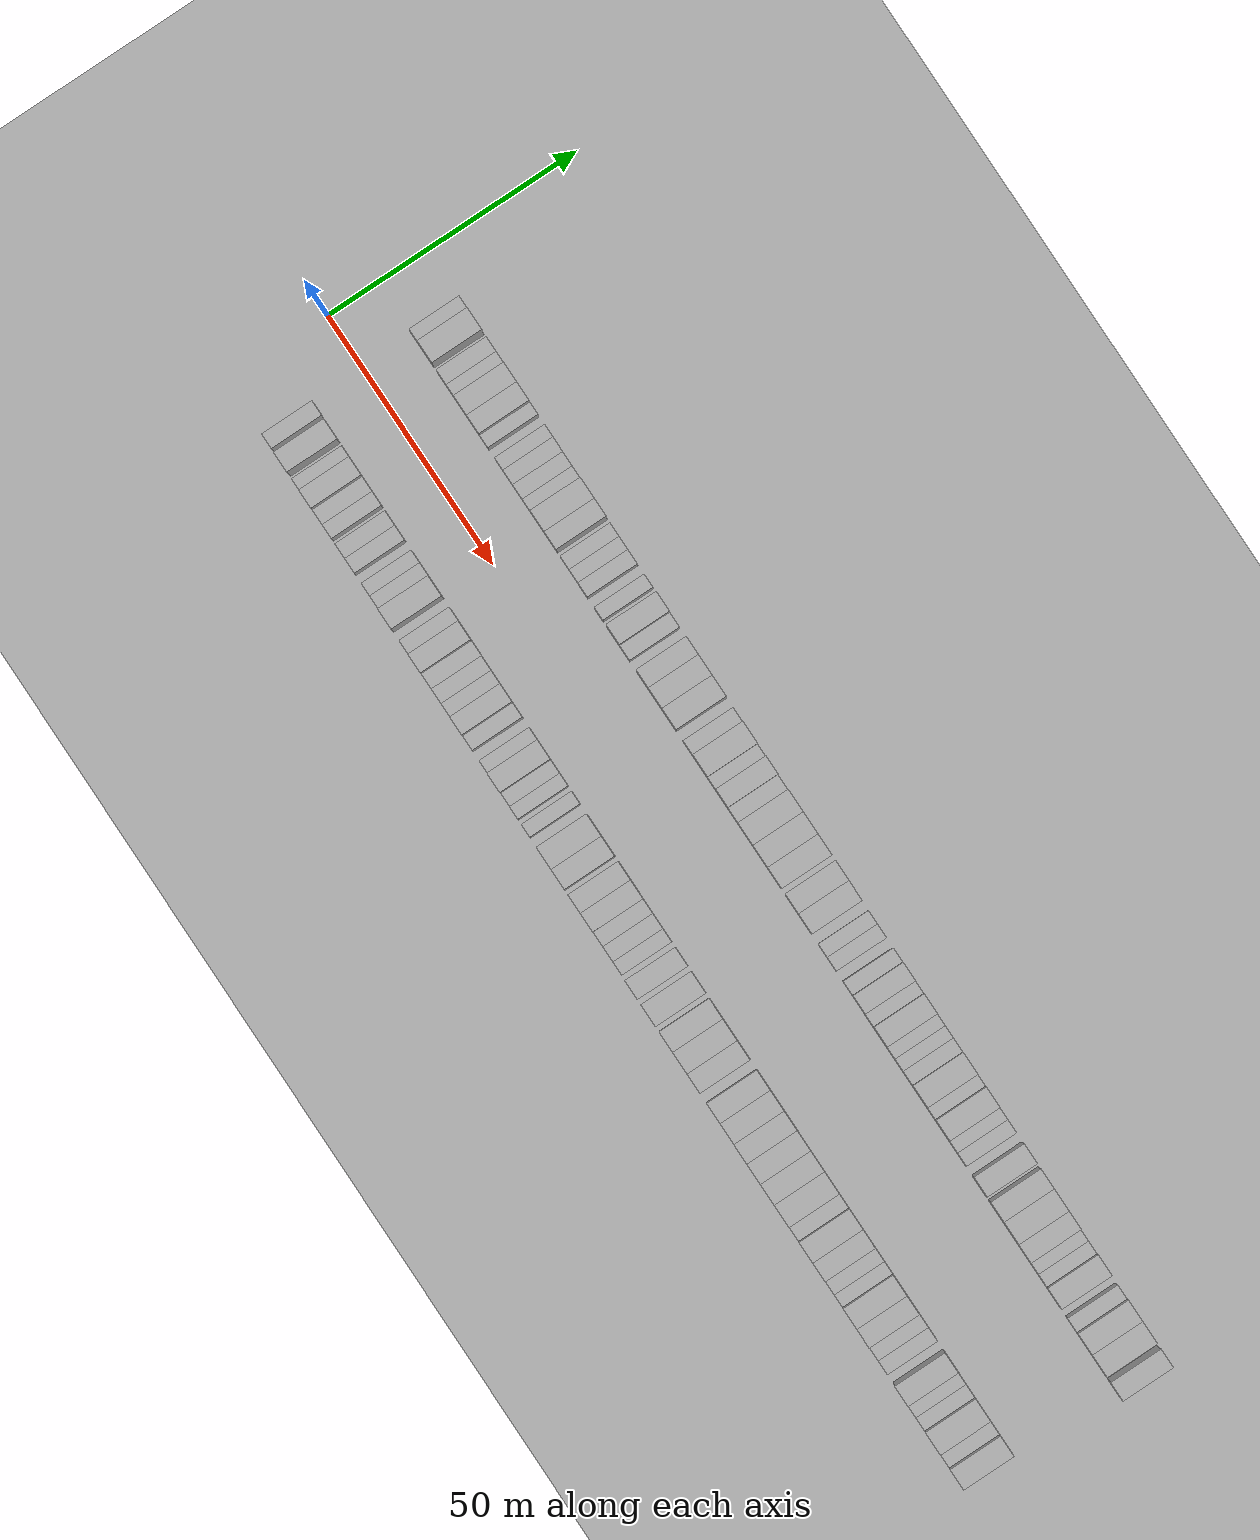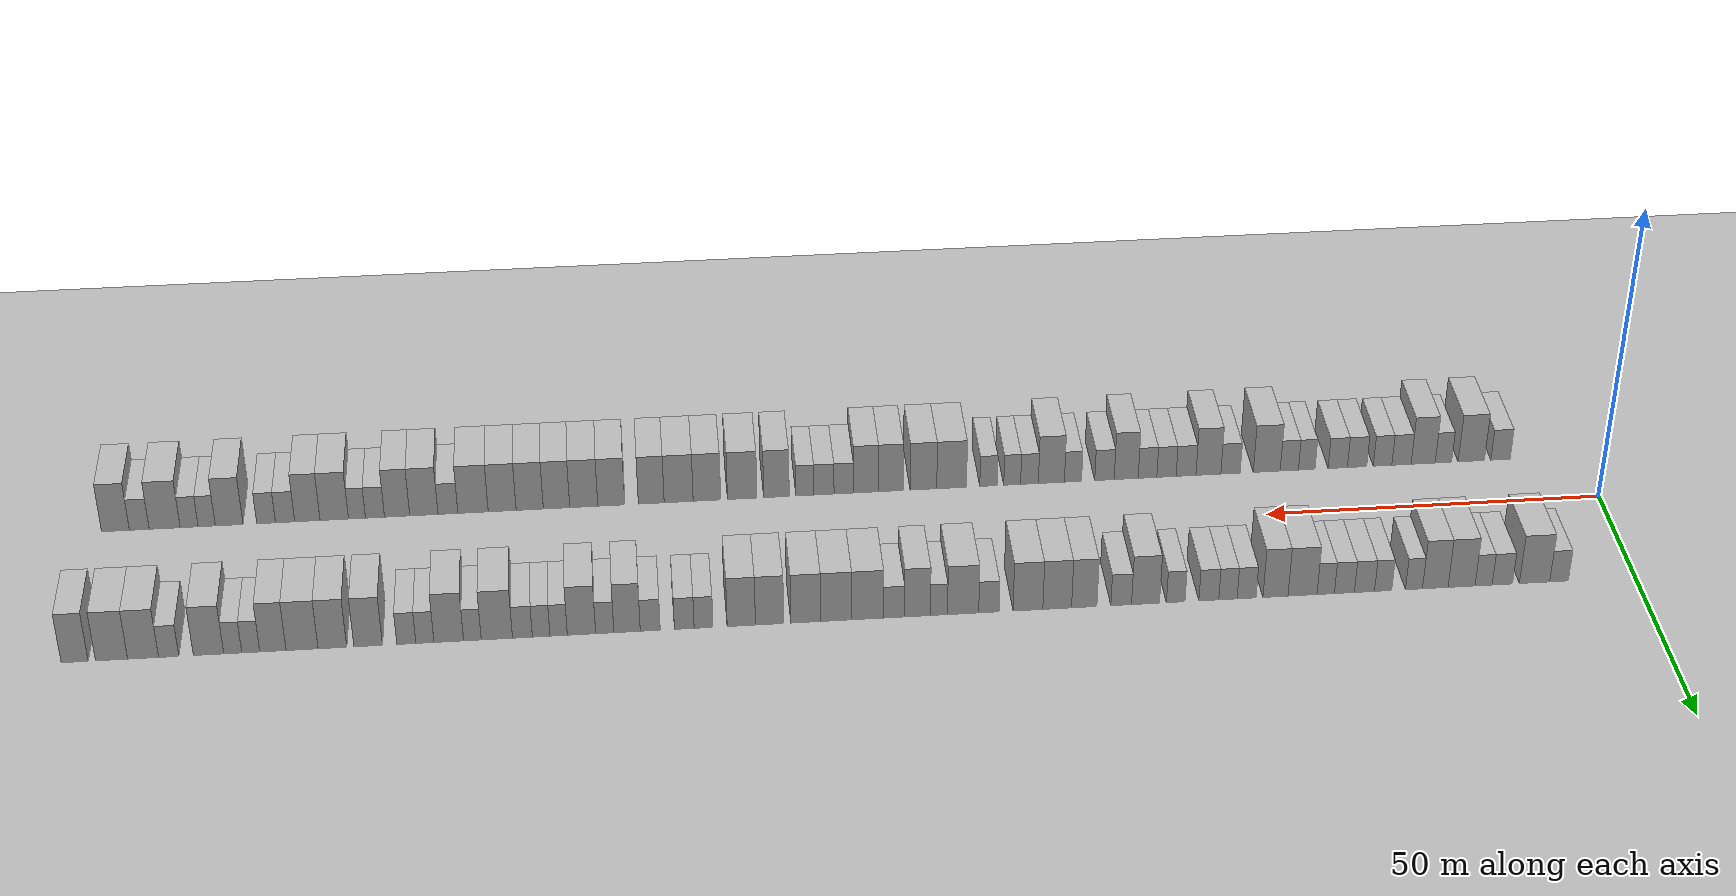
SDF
<?xml version="1.0" encoding="utf-8"?>

<sdf version="1.6">

   <world name="default">

      <gui fullscreen="0">

         <camera name="user_camera">

            <pose>-15 0 4.57585 0 0 0</pose>

            <view_controller>orbit</view_controller>

         </camera>

      </gui>

      <scene>

         <sky>

           <clouds>

             <speed>12</speed>

           </clouds>

         </sky>

         <ambient>0.4 0.4 0.4 1</ambient>

         <background>0.7 0.7 0.7 1</background>

         <shadows>1</shadows>

      </scene>

      <gravity>0 0 -9.8066</gravity>

      <magnetic_field>6e-06 2.3e-05 -4.2e-05</magnetic_field>

      <physics default="0" name="default_physics" type="ode">

         <ode>

            <solver>

               <type>quick</type>

               <iters>10</iters>

               <sor>1.0</sor>

               <use_dynamic_moi_rescaling>0</use_dynamic_moi_rescaling>

            </solver>

            <constraints>

               <cfm>0</cfm>

               <erp>0.2</erp>

               <contact_max_correcting_vel>100</contact_max_correcting_vel>

               <contact_surface_layer>0.001</contact_surface_layer>

            </constraints>

         </ode>

         <max_step_size>0.004</max_step_size>

         <real_time_factor>1</real_time_factor>

         <real_time_update_rate>250</real_time_update_rate>

      </physics>

      <light name="sun" type="directional">

         <cast_shadows>1</cast_shadows>

         <pose>0 0 10 0 0 0</pose>

         <diffuse>0.8 0.8 0.8 1</diffuse>

         <specular>0.2 0.2 0.2 1</specular>

         <attenuation>

            <range>1000</range>

            <constant>0.9</constant>

            <linear>0.01</linear>

            <quadratic>0.001</quadratic>

         </attenuation>

         <direction>-0.5 0.1 -0.9</direction>

      </light>

      <include>

         <name>ground_plane_1</name>

         <uri>model://HANNAS_ground_plane</uri>

         <pose>0 0 0  0 0 0</pose>

      </include>

      <include>

         <name>ground_plane_2</name>

         <uri>model://HANNAS_ground_plane</uri>

         <pose>100 0 0  0 0 0</pose>

      </include>

      <model name="building_1">

         <static>1</static>

         <pose frame="">11.3570 15.0000 0 0.000000 0.000000 1.570796</pose>

         <link name="link">

            <pose frame="">0 0 3.00 0 0 0</pose>

            <collision name="collision">

               <geometry>

                  <box>

                     <size>10.0000 2.7139 6.0000</size>

                  </box>

               </geometry>

               <max_contacts>10</max_contacts>

               <surface>

                  <contact>

                     <ode/>

                  </contact>

                  <bounce/>

                  <friction>

                     <torsional>

                        <ode/>

                     </torsional>

                     <ode/>

                  </friction>

               </surface>

            </collision>

            <visual name="visual">

               <cast_shadows>0</cast_shadows>

               <geometry>

                  <box>

                     <size>10.0000 2.7139 6.0000</size>

                  </box>

               </geometry>

               <material>

                  <script>

                     <uri>model://HANNAS_wall/materials/scripts</uri>

                     <uri>model://HANNAS_wall/materials/textures</uri>

                     <name>vrc/HANNAS_wall</name>

                  </script>

               </material>

            </visual>

            <self_collide>0</self_collide>

            <enable_wind>0</enable_wind>

            <kinematic>0</kinematic>

         </link>

      </model>

      <model name="building_2">

         <static>1</static>

         <pose frame="">14.9309 15.0000 0 0.000000 0.000000 1.570796</pose>

         <link name="link">

            <pose frame="">0 0 4.50 0 0 0</pose>

            <collision name="collision">

               <geometry>

                  <box>

                     <size>10.0000 4.4339 9.0000</size>

                  </box>

               </geometry>

               <max_contacts>10</max_contacts>

               <surface>

                  <contact>

                     <ode/>

                  </contact>

                  <bounce/>

                  <friction>

                     <torsional>

                        <ode/>

                     </torsional>

                     <ode/>

                  </friction>

               </surface>

            </collision>

            <visual name="visual">

               <cast_shadows>0</cast_shadows>

               <geometry>

                  <box>

                     <size>10.0000 4.4339 9.0000</size>

                  </box>

               </geometry>

               <material>

                  <script>

                     <uri>model://HANNAS_wall/materials/scripts</uri>

                     <uri>model://HANNAS_wall/materials/textures</uri>

                     <name>vrc/HANNAS_wall</name>

                  </script>

               </material>

            </visual>

            <self_collide>0</self_collide>

            <enable_wind>0</enable_wind>

            <kinematic>0</kinematic>

         </link>

      </model>

      <model name="building_3">

         <static>1</static>

         <pose frame="">19.6361 15.0000 0 0.000000 0.000000 1.570796</pose>

         <link name="link">

            <pose frame="">0 0 3.00 0 0 0</pose>

            <collision name="collision">

               <geometry>

                  <box>

                     <size>10.0000 2.9767 6.0000</size>

                  </box>

               </geometry>

               <max_contacts>10</max_contacts>

               <surface>

                  <contact>

                     <ode/>

                  </contact>

                  <bounce/>

                  <friction>

                     <torsional>

                        <ode/>

                     </torsional>

                     <ode/>

                  </friction>

               </surface>

            </collision>

            <visual name="visual">

               <cast_shadows>0</cast_shadows>

               <geometry>

                  <box>

                     <size>10.0000 2.9767 6.0000</size>

                  </box>

               </geometry>

               <material>

                  <script>

                     <uri>model://HANNAS_wall/materials/scripts</uri>

                     <uri>model://HANNAS_wall/materials/textures</uri>

                     <name>vrc/HANNAS_wall</name>

                  </script>

               </material>

            </visual>

            <self_collide>0</self_collide>

            <enable_wind>0</enable_wind>

            <kinematic>0</kinematic>

         </link>

      </model>

      <model name="building_4">

         <static>1</static>

         <pose frame="">22.3674 15.0000 0 0.000000 0.000000 1.570796</pose>

         <link name="link">

            <pose frame="">0 0 3.00 0 0 0</pose>

            <collision name="collision">

               <geometry>

                  <box>

                     <size>10.0000 2.4858 6.0000</size>

                  </box>

               </geometry>

               <max_contacts>10</max_contacts>

               <surface>

                  <contact>

                     <ode/>

                  </contact>

                  <bounce/>

                  <friction>

                     <torsional>

                        <ode/>

                     </torsional>

                     <ode/>

                  </friction>

               </surface>

            </collision>

            <visual name="visual">

               <cast_shadows>0</cast_shadows>

               <geometry>

                  <box>

                     <size>10.0000 2.4858 6.0000</size>

                  </box>

               </geometry>

               <material>

                  <script>

                     <uri>model://HANNAS_wall/materials/scripts</uri>

                     <uri>model://HANNAS_wall/materials/textures</uri>

                     <name>vrc/HANNAS_wall</name>

                  </script>

               </material>

            </visual>

            <self_collide>0</self_collide>

            <enable_wind>0</enable_wind>

            <kinematic>0</kinematic>

         </link>

      </model>

      <model name="building_5">

         <static>1</static>

         <pose frame="">25.5686 15.0000 0 0.000000 0.000000 1.570796</pose>

         <link name="link">

            <pose frame="">0 0 4.50 0 0 0</pose>

            <collision name="collision">

               <geometry>

                  <box>

                     <size>10.0000 3.9167 9.0000</size>

                  </box>

               </geometry>

               <max_contacts>10</max_contacts>

               <surface>

                  <contact>

                     <ode/>

                  </contact>

                  <bounce/>

                  <friction>

                     <torsional>

                        <ode/>

                     </torsional>

                     <ode/>

                  </friction>

               </surface>

            </collision>

            <visual name="visual">

               <cast_shadows>0</cast_shadows>

               <geometry>

                  <box>

                     <size>10.0000 3.9167 9.0000</size>

                  </box>

               </geometry>

               <material>

                  <script>

                     <uri>model://HANNAS_wall/materials/scripts</uri>

                     <uri>model://HANNAS_wall/materials/textures</uri>

                     <name>vrc/HANNAS_wall</name>

                  </script>

               </material>

            </visual>

            <self_collide>0</self_collide>

            <enable_wind>0</enable_wind>

            <kinematic>0</kinematic>

         </link>

      </model>

      <model name="building_6">

         <static>1</static>

         <pose frame="">29.3910 15.0000 0 0.000000 0.000000 1.570796</pose>

         <link name="link">

            <pose frame="">0 0 4.50 0 0 0</pose>

            <collision name="collision">

               <geometry>

                  <box>

                     <size>10.0000 3.7280 9.0000</size>

                  </box>

               </geometry>

               <max_contacts>10</max_contacts>

               <surface>

                  <contact>

                     <ode/>

                  </contact>

                  <bounce/>

                  <friction>

                     <torsional>

                        <ode/>

                     </torsional>

                     <ode/>

                  </friction>

               </surface>

            </collision>

            <visual name="visual">

               <cast_shadows>0</cast_shadows>

               <geometry>

                  <box>

                     <size>10.0000 3.7280 9.0000</size>

                  </box>

               </geometry>

               <material>

                  <script>

                     <uri>model://HANNAS_wall/materials/scripts</uri>

                     <uri>model://HANNAS_wall/materials/textures</uri>

                     <name>vrc/HANNAS_wall</name>

                  </script>

               </material>

            </visual>

            <self_collide>0</self_collide>

            <enable_wind>0</enable_wind>

            <kinematic>0</kinematic>

         </link>

      </model>

      <model name="building_7">

         <static>1</static>

         <pose frame="">32.4861 15.0000 0 0.000000 0.000000 1.570796</pose>

         <link name="link">

            <pose frame="">0 0 3.00 0 0 0</pose>

            <collision name="collision">

               <geometry>

                  <box>

                     <size>10.0000 2.4624 6.0000</size>

                  </box>

               </geometry>

               <max_contacts>10</max_contacts>

               <surface>

                  <contact>

                     <ode/>

                  </contact>

                  <bounce/>

                  <friction>

                     <torsional>

                        <ode/>

                     </torsional>

                     <ode/>

                  </friction>

               </surface>

            </collision>

            <visual name="visual">

               <cast_shadows>0</cast_shadows>

               <geometry>

                  <box>

                     <size>10.0000 2.4624 6.0000</size>

                  </box>

               </geometry>

               <material>

                  <script>

                     <uri>model://HANNAS_wall/materials/scripts</uri>

                     <uri>model://HANNAS_wall/materials/textures</uri>

                     <name>vrc/HANNAS_wall</name>

                  </script>

               </material>

            </visual>

            <self_collide>0</self_collide>

            <enable_wind>0</enable_wind>

            <kinematic>0</kinematic>

         </link>

      </model>

      <model name="building_8">

         <static>1</static>

         <pose frame="">36.9637 15.0000 0 0.000000 0.000000 1.570796</pose>

         <link name="link">

            <pose frame="">0 0 3.00 0 0 0</pose>

            <collision name="collision">

               <geometry>

                  <box>

                     <size>10.0000 2.4927 6.0000</size>

                  </box>

               </geometry>

               <max_contacts>10</max_contacts>

               <surface>

                  <contact>

                     <ode/>

                  </contact>

                  <bounce/>

                  <friction>

                     <torsional>

                        <ode/>

                     </torsional>

                     <ode/>

                  </friction>

               </surface>

            </collision>

            <visual name="visual">

               <cast_shadows>0</cast_shadows>

               <geometry>

                  <box>

                     <size>10.0000 2.4927 6.0000</size>

                  </box>

               </geometry>

               <material>

                  <script>

                     <uri>model://HANNAS_wall/materials/scripts</uri>

                     <uri>model://HANNAS_wall/materials/textures</uri>

                     <name>vrc/HANNAS_wall</name>

                  </script>

               </material>

            </visual>

            <self_collide>0</self_collide>

            <enable_wind>0</enable_wind>

            <kinematic>0</kinematic>

         </link>

      </model>

      <model name="building_9">

         <static>1</static>

         <pose frame="">39.6702 15.0000 0 0.000000 0.000000 1.570796</pose>

         <link name="link">

            <pose frame="">0 0 3.00 0 0 0</pose>

            <collision name="collision">

               <geometry>

                  <box>

                     <size>10.0000 2.9204 6.0000</size>

                  </box>

               </geometry>

               <max_contacts>10</max_contacts>

               <surface>

                  <contact>

                     <ode/>

                  </contact>

                  <bounce/>

                  <friction>

                     <torsional>

                        <ode/>

                     </torsional>

                     <ode/>

                  </friction>

               </surface>

            </collision>

            <visual name="visual">

               <cast_shadows>0</cast_shadows>

               <geometry>

                  <box>

                     <size>10.0000 2.9204 6.0000</size>

                  </box>

               </geometry>

               <material>

                  <script>

                     <uri>model://HANNAS_wall/materials/scripts</uri>

                     <uri>model://HANNAS_wall/materials/textures</uri>

                     <name>vrc/HANNAS_wall</name>

                  </script>

               </material>

            </visual>

            <self_collide>0</self_collide>

            <enable_wind>0</enable_wind>

            <kinematic>0</kinematic>

         </link>

      </model>

      <model name="building_10">

         <static>1</static>

         <pose frame="">42.5760 15.0000 0 0.000000 0.000000 1.570796</pose>

         <link name="link">

            <pose frame="">0 0 3.00 0 0 0</pose>

            <collision name="collision">

               <geometry>

                  <box>

                     <size>10.0000 2.8912 6.0000</size>

                  </box>

               </geometry>

               <max_contacts>10</max_contacts>

               <surface>

                  <contact>

                     <ode/>

                  </contact>

                  <bounce/>

                  <friction>

                     <torsional>

                        <ode/>

                     </torsional>

                     <ode/>

                  </friction>

               </surface>

            </collision>

            <visual name="visual">

               <cast_shadows>0</cast_shadows>

               <geometry>

                  <box>

                     <size>10.0000 2.8912 6.0000</size>

                  </box>

               </geometry>

               <material>

                  <script>

                     <uri>model://HANNAS_wall/materials/scripts</uri>

                     <uri>model://HANNAS_wall/materials/textures</uri>

                     <name>vrc/HANNAS_wall</name>

                  </script>

               </material>

            </visual>

            <self_collide>0</self_collide>

            <enable_wind>0</enable_wind>

            <kinematic>0</kinematic>

         </link>

      </model>

      <model name="building_11">

         <static>1</static>

         <pose frame="">45.2801 15.0000 0 0.000000 0.000000 1.570796</pose>

         <link name="link">

            <pose frame="">0 0 3.00 0 0 0</pose>

            <collision name="collision">

               <geometry>

                  <box>

                     <size>10.0000 2.5170 6.0000</size>

                  </box>

               </geometry>

               <max_contacts>10</max_contacts>

               <surface>

                  <contact>

                     <ode/>

                  </contact>

                  <bounce/>

                  <friction>

                     <torsional>

                        <ode/>

                     </torsional>

                     <ode/>

                  </friction>

               </surface>

            </collision>

            <visual name="visual">

               <cast_shadows>0</cast_shadows>

               <geometry>

                  <box>

                     <size>10.0000 2.5170 6.0000</size>

                  </box>

               </geometry>

               <material>

                  <script>

                     <uri>model://HANNAS_wall/materials/scripts</uri>

                     <uri>model://HANNAS_wall/materials/textures</uri>

                     <name>vrc/HANNAS_wall</name>

                  </script>

               </material>

            </visual>

            <self_collide>0</self_collide>

            <enable_wind>0</enable_wind>

            <kinematic>0</kinematic>

         </link>

      </model>

      <model name="building_12">

         <static>1</static>

         <pose frame="">48.6344 15.0000 0 0.000000 0.000000 1.570796</pose>

         <link name="link">

            <pose frame="">0 0 4.50 0 0 0</pose>

            <collision name="collision">

               <geometry>

                  <box>

                     <size>10.0000 4.1915 9.0000</size>

                  </box>

               </geometry>

               <max_contacts>10</max_contacts>

               <surface>

                  <contact>

                     <ode/>

                  </contact>

                  <bounce/>

                  <friction>

                     <torsional>

                        <ode/>

                     </torsional>

                     <ode/>

                  </friction>

               </surface>

            </collision>

            <visual name="visual">

               <cast_shadows>0</cast_shadows>

               <geometry>

                  <box>

                     <size>10.0000 4.1915 9.0000</size>

                  </box>

               </geometry>

               <material>

                  <script>

                     <uri>model://HANNAS_wall/materials/scripts</uri>

                     <uri>model://HANNAS_wall/materials/textures</uri>

                     <name>vrc/HANNAS_wall</name>

                  </script>

               </material>

            </visual>

            <self_collide>0</self_collide>

            <enable_wind>0</enable_wind>

            <kinematic>0</kinematic>

         </link>

      </model>

      <model name="building_13">

         <static>1</static>

         <pose frame="">52.5369 15.0000 0 0.000000 0.000000 1.570796</pose>

         <link name="link">

            <pose frame="">0 0 4.50 0 0 0</pose>

            <collision name="collision">

               <geometry>

                  <box>

                     <size>10.0000 3.6136 9.0000</size>

                  </box>

               </geometry>

               <max_contacts>10</max_contacts>

               <surface>

                  <contact>

                     <ode/>

                  </contact>

                  <bounce/>

                  <friction>

                     <torsional>

                        <ode/>

                     </torsional>

                     <ode/>

                  </friction>

               </surface>

            </collision>

            <visual name="visual">

               <cast_shadows>0</cast_shadows>

               <geometry>

                  <box>

                     <size>10.0000 3.6136 9.0000</size>

                  </box>

               </geometry>

               <material>

                  <script>

                     <uri>model://HANNAS_wall/materials/scripts</uri>

                     <uri>model://HANNAS_wall/materials/textures</uri>

                     <name>vrc/HANNAS_wall</name>

                  </script>

               </material>

            </visual>

            <self_collide>0</self_collide>

            <enable_wind>0</enable_wind>

            <kinematic>0</kinematic>

         </link>

      </model>

      <model name="building_14">

         <static>1</static>

         <pose frame="">56.7094 15.0000 0 0.000000 0.000000 1.570796</pose>

         <link name="link">

            <pose frame="">0 0 3.00 0 0 0</pose>

            <collision name="collision">

               <geometry>

                  <box>

                     <size>10.0000 2.7313 6.0000</size>

                  </box>

               </geometry>

               <max_contacts>10</max_contacts>

               <surface>

                  <contact>

                     <ode/>

                  </contact>

                  <bounce/>

                  <friction>

                     <torsional>

                        <ode/>

                     </torsional>

                     <ode/>

                  </friction>

               </surface>

            </collision>

            <visual name="visual">

               <cast_shadows>0</cast_shadows>

               <geometry>

                  <box>

                     <size>10.0000 2.7313 6.0000</size>

                  </box>

               </geometry>

               <material>

                  <script>

                     <uri>model://HANNAS_wall/materials/scripts</uri>

                     <uri>model://HANNAS_wall/materials/textures</uri>

                     <name>vrc/HANNAS_wall</name>

                  </script>

               </material>

            </visual>

            <self_collide>0</self_collide>

            <enable_wind>0</enable_wind>

            <kinematic>0</kinematic>

         </link>

      </model>

      <model name="building_15">

         <static>1</static>

         <pose frame="">59.3927 15.0000 0 0.000000 0.000000 1.570796</pose>

         <link name="link">

            <pose frame="">0 0 3.00 0 0 0</pose>

            <collision name="collision">

               <geometry>

                  <box>

                     <size>10.0000 2.6354 6.0000</size>

                  </box>

               </geometry>

               <max_contacts>10</max_contacts>

               <surface>

                  <contact>

                     <ode/>

                  </contact>

                  <bounce/>

                  <friction>

                     <torsional>

                        <ode/>

                     </torsional>

                     <ode/>

                  </friction>

               </surface>

            </collision>

            <visual name="visual">

               <cast_shadows>0</cast_shadows>

               <geometry>

                  <box>

                     <size>10.0000 2.6354 6.0000</size>

                  </box>

               </geometry>

               <material>

                  <script>

                     <uri>model://HANNAS_wall/materials/scripts</uri>

                     <uri>model://HANNAS_wall/materials/textures</uri>

                     <name>vrc/HANNAS_wall</name>

                  </script>

               </material>

            </visual>

            <self_collide>0</self_collide>

            <enable_wind>0</enable_wind>

            <kinematic>0</kinematic>

         </link>

      </model>

      <model name="building_16">

         <static>1</static>

         <pose frame="">62.1425 15.0000 0 0.000000 0.000000 1.570796</pose>

         <link name="link">

            <pose frame="">0 0 3.00 0 0 0</pose>

            <collision name="collision">

               <geometry>

                  <box>

                     <size>10.0000 2.8643 6.0000</size>

                  </box>

               </geometry>

               <max_contacts>10</max_contacts>

               <surface>

                  <contact>

                     <ode/>

                  </contact>

                  <bounce/>

                  <friction>

                     <torsional>

                        <ode/>

                     </torsional>

                     <ode/>

                  </friction>

               </surface>

            </collision>

            <visual name="visual">

               <cast_shadows>0</cast_shadows>

               <geometry>

                  <box>

                     <size>10.0000 2.8643 6.0000</size>

                  </box>

               </geometry>

               <material>

                  <script>

                     <uri>model://HANNAS_wall/materials/scripts</uri>

                     <uri>model://HANNAS_wall/materials/textures</uri>

                     <name>vrc/HANNAS_wall</name>

                  </script>

               </material>

            </visual>

            <self_collide>0</self_collide>

            <enable_wind>0</enable_wind>

            <kinematic>0</kinematic>

         </link>

      </model>

      <model name="building_17">

         <static>1</static>

         <pose frame="">66.9048 15.0000 0 0.000000 0.000000 1.570796</pose>

         <link name="link">

            <pose frame="">0 0 3.00 0 0 0</pose>

            <collision name="collision">

               <geometry>

                  <box>

                     <size>10.0000 2.6602 6.0000</size>

                  </box>

               </geometry>

               <max_contacts>10</max_contacts>

               <surface>

                  <contact>

                     <ode/>

                  </contact>

                  <bounce/>

                  <friction>

                     <torsional>

                        <ode/>

                     </torsional>

                     <ode/>

                  </friction>

               </surface>

            </collision>

            <visual name="visual">

               <cast_shadows>0</cast_shadows>

               <geometry>

                  <box>

                     <size>10.0000 2.6602 6.0000</size>

                  </box>

               </geometry>

               <material>

                  <script>

                     <uri>model://HANNAS_wall/materials/scripts</uri>

                     <uri>model://HANNAS_wall/materials/textures</uri>

                     <name>vrc/HANNAS_wall</name>

                  </script>

               </material>

            </visual>

            <self_collide>0</self_collide>

            <enable_wind>0</enable_wind>

            <kinematic>0</kinematic>

         </link>

      </model>

      <model name="building_18">

         <static>1</static>

         <pose frame="">71.2412 15.0000 0 0.000000 0.000000 1.570796</pose>

         <link name="link">

            <pose frame="">0 0 4.50 0 0 0</pose>

            <collision name="collision">

               <geometry>

                  <box>

                     <size>10.0000 4.0127 9.0000</size>

                  </box>

               </geometry>

               <max_contacts>10</max_contacts>

               <surface>

                  <contact>

                     <ode/>

                  </contact>

                  <bounce/>

                  <friction>

                     <torsional>

                        <ode/>

                     </torsional>

                     <ode/>

                  </friction>

               </surface>

            </collision>

            <visual name="visual">

               <cast_shadows>0</cast_shadows>

               <geometry>

                  <box>

                     <size>10.0000 4.0127 9.0000</size>

                  </box>

               </geometry>

               <material>

                  <script>

                     <uri>model://HANNAS_wall/materials/scripts</uri>

                     <uri>model://HANNAS_wall/materials/textures</uri>

                     <name>vrc/HANNAS_wall</name>

                  </script>

               </material>

            </visual>

            <self_collide>0</self_collide>

            <enable_wind>0</enable_wind>

            <kinematic>0</kinematic>

         </link>

      </model>

      <model name="building_19">

         <static>1</static>

         <pose frame="">74.7267 15.0000 0 0.000000 0.000000 1.570796</pose>

         <link name="link">

            <pose frame="">0 0 3.00 0 0 0</pose>

            <collision name="collision">

               <geometry>

                  <box>

                     <size>10.0000 2.9582 6.0000</size>

                  </box>

               </geometry>

               <max_contacts>10</max_contacts>

               <surface>

                  <contact>

                     <ode/>

                  </contact>

                  <bounce/>

                  <friction>

                     <torsional>

                        <ode/>

                     </torsional>

                     <ode/>

                  </friction>

               </surface>

            </collision>

            <visual name="visual">

               <cast_shadows>0</cast_shadows>

               <geometry>

                  <box>

                     <size>10.0000 2.9582 6.0000</size>

                  </box>

               </geometry>

               <material>

                  <script>

                     <uri>model://HANNAS_wall/materials/scripts</uri>

                     <uri>model://HANNAS_wall/materials/textures</uri>

                     <name>vrc/HANNAS_wall</name>

                  </script>

               </material>

            </visual>

            <self_collide>0</self_collide>

            <enable_wind>0</enable_wind>

            <kinematic>0</kinematic>

         </link>

      </model>

      <model name="building_20">

         <static>1</static>

         <pose frame="">80.0178 15.0000 0 0.000000 0.000000 1.570796</pose>

         <link name="link">

            <pose frame="">0 0 4.50 0 0 0</pose>

            <collision name="collision">

               <geometry>

                  <box>

                     <size>10.0000 3.6240 9.0000</size>

                  </box>

               </geometry>

               <max_contacts>10</max_contacts>

               <surface>

                  <contact>

                     <ode/>

                  </contact>

                  <bounce/>

                  <friction>

                     <torsional>

                        <ode/>

                     </torsional>

                     <ode/>

                  </friction>

               </surface>

            </collision>

            <visual name="visual">

               <cast_shadows>0</cast_shadows>

               <geometry>

                  <box>

                     <size>10.0000 3.6240 9.0000</size>

                  </box>

               </geometry>

               <material>

                  <script>

                     <uri>model://HANNAS_wall/materials/scripts</uri>

                     <uri>model://HANNAS_wall/materials/textures</uri>

                     <name>vrc/HANNAS_wall</name>

                  </script>

               </material>

            </visual>

            <self_collide>0</self_collide>

            <enable_wind>0</enable_wind>

            <kinematic>0</kinematic>

         </link>

      </model>

      <model name="building_21">

         <static>1</static>

         <pose frame="">83.8820 15.0000 0 0.000000 0.000000 1.570796</pose>

         <link name="link">

            <pose frame="">0 0 4.50 0 0 0</pose>

            <collision name="collision">

               <geometry>

                  <box>

                     <size>10.0000 4.1045 9.0000</size>

                  </box>

               </geometry>

               <max_contacts>10</max_contacts>

               <surface>

                  <contact>

                     <ode/>

                  </contact>

                  <bounce/>

                  <friction>

                     <torsional>

                        <ode/>

                     </torsional>

                     <ode/>

                  </friction>

               </surface>

            </collision>

            <visual name="visual">

               <cast_shadows>0</cast_shadows>

               <geometry>

                  <box>

                     <size>10.0000 4.1045 9.0000</size>

                  </box>

               </geometry>

               <material>

                  <script>

                     <uri>model://HANNAS_wall/materials/scripts</uri>

                     <uri>model://HANNAS_wall/materials/textures</uri>

                     <name>vrc/HANNAS_wall</name>

                  </script>

               </material>

            </visual>

            <self_collide>0</self_collide>

            <enable_wind>0</enable_wind>

            <kinematic>0</kinematic>

         </link>

      </model>

      <model name="building_22">

         <static>1</static>

         <pose frame="">88.0626 15.0000 0 0.000000 0.000000 1.570796</pose>

         <link name="link">

            <pose frame="">0 0 4.50 0 0 0</pose>

            <collision name="collision">

               <geometry>

                  <box>

                     <size>10.0000 4.2569 9.0000</size>

                  </box>

               </geometry>

               <max_contacts>10</max_contacts>

               <surface>

                  <contact>

                     <ode/>

                  </contact>

                  <bounce/>

                  <friction>

                     <torsional>

                        <ode/>

                     </torsional>

                     <ode/>

                  </friction>

               </surface>

            </collision>

            <visual name="visual">

               <cast_shadows>0</cast_shadows>

               <geometry>

                  <box>

                     <size>10.0000 4.2569 9.0000</size>

                  </box>

               </geometry>

               <material>

                  <script>

                     <uri>model://HANNAS_wall/materials/scripts</uri>

                     <uri>model://HANNAS_wall/materials/textures</uri>

                     <name>vrc/HANNAS_wall</name>

                  </script>

               </material>

            </visual>

            <self_collide>0</self_collide>

            <enable_wind>0</enable_wind>

            <kinematic>0</kinematic>

         </link>

      </model>

      <model name="building_23">

         <static>1</static>

         <pose frame="">93.6376 15.0000 0 0.000000 0.000000 1.570796</pose>

         <link name="link">

            <pose frame="">0 0 3.00 0 0 0</pose>

            <collision name="collision">

               <geometry>

                  <box>

                     <size>10.0000 2.8930 6.0000</size>

                  </box>

               </geometry>

               <max_contacts>10</max_contacts>

               <surface>

                  <contact>

                     <ode/>

                  </contact>

                  <bounce/>

                  <friction>

                     <torsional>

                        <ode/>

                     </torsional>

                     <ode/>

                  </friction>

               </surface>

            </collision>

            <visual name="visual">

               <cast_shadows>0</cast_shadows>

               <geometry>

                  <box>

                     <size>10.0000 2.8930 6.0000</size>

                  </box>

               </geometry>

               <material>

                  <script>

                     <uri>model://HANNAS_wall/materials/scripts</uri>

                     <uri>model://HANNAS_wall/materials/textures</uri>

                     <name>vrc/HANNAS_wall</name>

                  </script>

               </material>

            </visual>

            <self_collide>0</self_collide>

            <enable_wind>0</enable_wind>

            <kinematic>0</kinematic>

         </link>

      </model>

      <model name="building_24">

         <static>1</static>

         <pose frame="">97.3048 15.0000 0 0.000000 0.000000 1.570796</pose>

         <link name="link">

            <pose frame="">0 0 4.50 0 0 0</pose>

            <collision name="collision">

               <geometry>

                  <box>

                     <size>10.0000 4.4415 9.0000</size>

                  </box>

               </geometry>

               <max_contacts>10</max_contacts>

               <surface>

                  <contact>

                     <ode/>

                  </contact>

                  <bounce/>

                  <friction>

                     <torsional>

                        <ode/>

                     </torsional>

                     <ode/>

                  </friction>

               </surface>

            </collision>

            <visual name="visual">

               <cast_shadows>0</cast_shadows>

               <geometry>

                  <box>

                     <size>10.0000 4.4415 9.0000</size>

                  </box>

               </geometry>

               <material>

                  <script>

                     <uri>model://HANNAS_wall/materials/scripts</uri>

                     <uri>model://HANNAS_wall/materials/textures</uri>

                     <name>vrc/HANNAS_wall</name>

                  </script>

               </material>

            </visual>

            <self_collide>0</self_collide>

            <enable_wind>0</enable_wind>

            <kinematic>0</kinematic>

         </link>

      </model>

      <model name="building_25">

         <static>1</static>

         <pose frame="">100.7398 15.0000 0 0.000000 0.000000 1.570796</pose>

         <link name="link">

            <pose frame="">0 0 3.00 0 0 0</pose>

            <collision name="collision">

               <geometry>

                  <box>

                     <size>10.0000 2.4285 6.0000</size>

                  </box>

               </geometry>

               <max_contacts>10</max_contacts>

               <surface>

                  <contact>

                     <ode/>

                  </contact>

                  <bounce/>

                  <friction>

                     <torsional>

                        <ode/>

                     </torsional>

                     <ode/>

                  </friction>

               </surface>

            </collision>

            <visual name="visual">

               <cast_shadows>0</cast_shadows>

               <geometry>

                  <box>

                     <size>10.0000 2.4285 6.0000</size>

                  </box>

               </geometry>

               <material>

                  <script>

                     <uri>model://HANNAS_wall/materials/scripts</uri>

                     <uri>model://HANNAS_wall/materials/textures</uri>

                     <name>vrc/HANNAS_wall</name>

                  </script>

               </material>

            </visual>

            <self_collide>0</self_collide>

            <enable_wind>0</enable_wind>

            <kinematic>0</kinematic>

         </link>

      </model>

      <model name="building_26">

         <static>1</static>

         <pose frame="">103.7903 15.0000 0 0.000000 0.000000 1.570796</pose>

         <link name="link">

            <pose frame="">0 0 4.50 0 0 0</pose>

            <collision name="collision">

               <geometry>

                  <box>

                     <size>10.0000 3.6724 9.0000</size>

                  </box>

               </geometry>

               <max_contacts>10</max_contacts>

               <surface>

                  <contact>

                     <ode/>

                  </contact>

                  <bounce/>

                  <friction>

                     <torsional>

                        <ode/>

                     </torsional>

                     <ode/>

                  </friction>

               </surface>

            </collision>

            <visual name="visual">

               <cast_shadows>0</cast_shadows>

               <geometry>

                  <box>

                     <size>10.0000 3.6724 9.0000</size>

                  </box>

               </geometry>

               <material>

                  <script>

                     <uri>model://HANNAS_wall/materials/scripts</uri>

                     <uri>model://HANNAS_wall/materials/textures</uri>

                     <name>vrc/HANNAS_wall</name>

                  </script>

               </material>

            </visual>

            <self_collide>0</self_collide>

            <enable_wind>0</enable_wind>

            <kinematic>0</kinematic>

         </link>

      </model>

      <model name="building_27">

         <static>1</static>

         <pose frame="">107.1217 15.0000 0 0.000000 0.000000 1.570796</pose>

         <link name="link">

            <pose frame="">0 0 3.00 0 0 0</pose>

            <collision name="collision">

               <geometry>

                  <box>

                     <size>10.0000 2.9904 6.0000</size>

                  </box>

               </geometry>

               <max_contacts>10</max_contacts>

               <surface>

                  <contact>

                     <ode/>

                  </contact>

                  <bounce/>

                  <friction>

                     <torsional>

                        <ode/>

                     </torsional>

                     <ode/>

                  </friction>

               </surface>

            </collision>

            <visual name="visual">

               <cast_shadows>0</cast_shadows>

               <geometry>

                  <box>

                     <size>10.0000 2.9904 6.0000</size>

                  </box>

               </geometry>

               <material>

                  <script>

                     <uri>model://HANNAS_wall/materials/scripts</uri>

                     <uri>model://HANNAS_wall/materials/textures</uri>

                     <name>vrc/HANNAS_wall</name>

                  </script>

               </material>

            </visual>

            <self_collide>0</self_collide>

            <enable_wind>0</enable_wind>

            <kinematic>0</kinematic>

         </link>

      </model>

      <model name="building_28">

         <static>1</static>

         <pose frame="">110.8591 15.0000 0 0.000000 0.000000 1.570796</pose>

         <link name="link">

            <pose frame="">0 0 4.50 0 0 0</pose>

            <collision name="collision">

               <geometry>

                  <box>

                     <size>10.0000 4.4845 9.0000</size>

                  </box>

               </geometry>

               <max_contacts>10</max_contacts>

               <surface>

                  <contact>

                     <ode/>

                  </contact>

                  <bounce/>

                  <friction>

                     <torsional>

                        <ode/>

                     </torsional>

                     <ode/>

                  </friction>

               </surface>

            </collision>

            <visual name="visual">

               <cast_shadows>0</cast_shadows>

               <geometry>

                  <box>

                     <size>10.0000 4.4845 9.0000</size>

                  </box>

               </geometry>

               <material>

                  <script>

                     <uri>model://HANNAS_wall/materials/scripts</uri>

                     <uri>model://HANNAS_wall/materials/textures</uri>

                     <name>vrc/HANNAS_wall</name>

                  </script>

               </material>

            </visual>

            <self_collide>0</self_collide>

            <enable_wind>0</enable_wind>

            <kinematic>0</kinematic>

         </link>

      </model>

      <model name="building_29">

         <static>1</static>

         <pose frame="">115.2992 15.0000 0 0.000000 0.000000 1.570796</pose>

         <link name="link">

            <pose frame="">0 0 4.50 0 0 0</pose>

            <collision name="collision">

               <geometry>

                  <box>

                     <size>10.0000 4.3955 9.0000</size>

                  </box>

               </geometry>

               <max_contacts>10</max_contacts>

               <surface>

                  <contact>

                     <ode/>

                  </contact>

                  <bounce/>

                  <friction>

                     <torsional>

                        <ode/>

                     </torsional>

                     <ode/>

                  </friction>

               </surface>

            </collision>

            <visual name="visual">

               <cast_shadows>0</cast_shadows>

               <geometry>

                  <box>

                     <size>10.0000 4.3955 9.0000</size>

                  </box>

               </geometry>

               <material>

                  <script>

                     <uri>model://HANNAS_wall/materials/scripts</uri>

                     <uri>model://HANNAS_wall/materials/textures</uri>

                     <name>vrc/HANNAS_wall</name>

                  </script>

               </material>

            </visual>

            <self_collide>0</self_collide>

            <enable_wind>0</enable_wind>

            <kinematic>0</kinematic>

         </link>

      </model>

      <model name="building_30">

         <static>1</static>

         <pose frame="">119.6165 15.0000 0 0.000000 0.000000 1.570796</pose>

         <link name="link">

            <pose frame="">0 0 4.50 0 0 0</pose>

            <collision name="collision">

               <geometry>

                  <box>

                     <size>10.0000 4.2392 9.0000</size>

                  </box>

               </geometry>

               <max_contacts>10</max_contacts>

               <surface>

                  <contact>

                     <ode/>

                  </contact>

                  <bounce/>

                  <friction>

                     <torsional>

                        <ode/>

                     </torsional>

                     <ode/>

                  </friction>

               </surface>

            </collision>

            <visual name="visual">

               <cast_shadows>0</cast_shadows>

               <geometry>

                  <box>

                     <size>10.0000 4.2392 9.0000</size>

                  </box>

               </geometry>

               <material>

                  <script>

                     <uri>model://HANNAS_wall/materials/scripts</uri>

                     <uri>model://HANNAS_wall/materials/textures</uri>

                     <name>vrc/HANNAS_wall</name>

                  </script>

               </material>

            </visual>

            <self_collide>0</self_collide>

            <enable_wind>0</enable_wind>

            <kinematic>0</kinematic>

         </link>

      </model>

      <model name="building_31">

         <static>1</static>

         <pose frame="">124.7347 15.0000 0 0.000000 0.000000 1.570796</pose>

         <link name="link">

            <pose frame="">0 0 4.50 0 0 0</pose>

            <collision name="collision">

               <geometry>

                  <box>

                     <size>10.0000 3.9970 9.0000</size>

                  </box>

               </geometry>

               <max_contacts>10</max_contacts>

               <surface>

                  <contact>

                     <ode/>

                  </contact>

                  <bounce/>

                  <friction>

                     <torsional>

                        <ode/>

                     </torsional>

                     <ode/>

                  </friction>

               </surface>

            </collision>

            <visual name="visual">

               <cast_shadows>0</cast_shadows>

               <geometry>

                  <box>

                     <size>10.0000 3.9970 9.0000</size>

                  </box>

               </geometry>

               <material>

                  <script>

                     <uri>model://HANNAS_wall/materials/scripts</uri>

                     <uri>model://HANNAS_wall/materials/textures</uri>

                     <name>vrc/HANNAS_wall</name>

                  </script>

               </material>

            </visual>

            <self_collide>0</self_collide>

            <enable_wind>0</enable_wind>

            <kinematic>0</kinematic>

         </link>

      </model>

      <model name="building_32">

         <static>1</static>

         <pose frame="">128.7281 15.0000 0 0.000000 0.000000 1.570796</pose>

         <link name="link">

            <pose frame="">0 0 4.50 0 0 0</pose>

            <collision name="collision">

               <geometry>

                  <box>

                     <size>10.0000 3.9899 9.0000</size>

                  </box>

               </geometry>

               <max_contacts>10</max_contacts>

               <surface>

                  <contact>

                     <ode/>

                  </contact>

                  <bounce/>

                  <friction>

                     <torsional>

                        <ode/>

                     </torsional>

                     <ode/>

                  </friction>

               </surface>

            </collision>

            <visual name="visual">

               <cast_shadows>0</cast_shadows>

               <geometry>

                  <box>

                     <size>10.0000 3.9899 9.0000</size>

                  </box>

               </geometry>

               <material>

                  <script>

                     <uri>model://HANNAS_wall/materials/scripts</uri>

                     <uri>model://HANNAS_wall/materials/textures</uri>

                     <name>vrc/HANNAS_wall</name>

                  </script>

               </material>

            </visual>

            <self_collide>0</self_collide>

            <enable_wind>0</enable_wind>

            <kinematic>0</kinematic>

         </link>

      </model>

      <model name="building_33">

         <static>1</static>

         <pose frame="">134.0501 15.0000 0 0.000000 0.000000 1.570796</pose>

         <link name="link">

            <pose frame="">0 0 3.00 0 0 0</pose>

            <collision name="collision">

               <geometry>

                  <box>

                     <size>10.0000 2.6541 6.0000</size>

                  </box>

               </geometry>

               <max_contacts>10</max_contacts>

               <surface>

                  <contact>

                     <ode/>

                  </contact>

                  <bounce/>

                  <friction>

                     <torsional>

                        <ode/>

                     </torsional>

                     <ode/>

                  </friction>

               </surface>

            </collision>

            <visual name="visual">

               <cast_shadows>0</cast_shadows>

               <geometry>

                  <box>

                     <size>10.0000 2.6541 6.0000</size>

                  </box>

               </geometry>

               <material>

                  <script>

                     <uri>model://HANNAS_wall/materials/scripts</uri>

                     <uri>model://HANNAS_wall/materials/textures</uri>

                     <name>vrc/HANNAS_wall</name>

                  </script>

               </material>

            </visual>

            <self_collide>0</self_collide>

            <enable_wind>0</enable_wind>

            <kinematic>0</kinematic>

         </link>

      </model>

      <model name="building_34">

         <static>1</static>

         <pose frame="">136.7619 15.0000 0 0.000000 0.000000 1.570796</pose>

         <link name="link">

            <pose frame="">0 0 3.00 0 0 0</pose>

            <collision name="collision">

               <geometry>

                  <box>

                     <size>10.0000 2.7695 6.0000</size>

                  </box>

               </geometry>

               <max_contacts>10</max_contacts>

               <surface>

                  <contact>

                     <ode/>

                  </contact>

                  <bounce/>

                  <friction>

                     <torsional>

                        <ode/>

                     </torsional>

                     <ode/>

                  </friction>

               </surface>

            </collision>

            <visual name="visual">

               <cast_shadows>0</cast_shadows>

               <geometry>

                  <box>

                     <size>10.0000 2.7695 6.0000</size>

                  </box>

               </geometry>

               <material>

                  <script>

                     <uri>model://HANNAS_wall/materials/scripts</uri>

                     <uri>model://HANNAS_wall/materials/textures</uri>

                     <name>vrc/HANNAS_wall</name>

                  </script>

               </material>

            </visual>

            <self_collide>0</self_collide>

            <enable_wind>0</enable_wind>

            <kinematic>0</kinematic>

         </link>

      </model>

      <model name="building_35">

         <static>1</static>

         <pose frame="">141.5453 15.0000 0 0.000000 0.000000 1.570796</pose>

         <link name="link">

            <pose frame="">0 0 3.00 0 0 0</pose>

            <collision name="collision">

               <geometry>

                  <box>

                     <size>10.0000 2.7974 6.0000</size>

                  </box>

               </geometry>

               <max_contacts>10</max_contacts>

               <surface>

                  <contact>

                     <ode/>

                  </contact>

                  <bounce/>

                  <friction>

                     <torsional>

                        <ode/>

                     </torsional>

                     <ode/>

                  </friction>

               </surface>

            </collision>

            <visual name="visual">

               <cast_shadows>0</cast_shadows>

               <geometry>

                  <box>

                     <size>10.0000 2.7974 6.0000</size>

                  </box>

               </geometry>

               <material>

                  <script>

                     <uri>model://HANNAS_wall/materials/scripts</uri>

                     <uri>model://HANNAS_wall/materials/textures</uri>

                     <name>vrc/HANNAS_wall</name>

                  </script>

               </material>

            </visual>

            <self_collide>0</self_collide>

            <enable_wind>0</enable_wind>

            <kinematic>0</kinematic>

         </link>

      </model>

      <model name="building_36">

         <static>1</static>

         <pose frame="">144.7961 15.0000 0 0.000000 0.000000 1.570796</pose>

         <link name="link">

            <pose frame="">0 0 4.50 0 0 0</pose>

            <collision name="collision">

               <geometry>

                  <box>

                     <size>10.0000 3.7042 9.0000</size>

                  </box>

               </geometry>

               <max_contacts>10</max_contacts>

               <surface>

                  <contact>

                     <ode/>

                  </contact>

                  <bounce/>

                  <friction>

                     <torsional>

                        <ode/>

                     </torsional>

                     <ode/>

                  </friction>

               </surface>

            </collision>

            <visual name="visual">

               <cast_shadows>0</cast_shadows>

               <geometry>

                  <box>

                     <size>10.0000 3.7042 9.0000</size>

                  </box>

               </geometry>

               <material>

                  <script>

                     <uri>model://HANNAS_wall/materials/scripts</uri>

                     <uri>model://HANNAS_wall/materials/textures</uri>

                     <name>vrc/HANNAS_wall</name>

                  </script>

               </material>

            </visual>

            <self_collide>0</self_collide>

            <enable_wind>0</enable_wind>

            <kinematic>0</kinematic>

         </link>

      </model>

      <model name="building_37">

         <static>1</static>

         <pose frame="">147.9257 15.0000 0 0.000000 0.000000 1.570796</pose>

         <link name="link">

            <pose frame="">0 0 3.00 0 0 0</pose>

            <collision name="collision">

               <geometry>

                  <box>

                     <size>10.0000 2.5549 6.0000</size>

                  </box>

               </geometry>

               <max_contacts>10</max_contacts>

               <surface>

                  <contact>

                     <ode/>

                  </contact>

                  <bounce/>

                  <friction>

                     <torsional>

                        <ode/>

                     </torsional>

                     <ode/>

                  </friction>

               </surface>

            </collision>

            <visual name="visual">

               <cast_shadows>0</cast_shadows>

               <geometry>

                  <box>

                     <size>10.0000 2.5549 6.0000</size>

                  </box>

               </geometry>

               <material>

                  <script>

                     <uri>model://HANNAS_wall/materials/scripts</uri>

                     <uri>model://HANNAS_wall/materials/textures</uri>

                     <name>vrc/HANNAS_wall</name>

                  </script>

               </material>

            </visual>

            <self_collide>0</self_collide>

            <enable_wind>0</enable_wind>

            <kinematic>0</kinematic>

         </link>

      </model>

      <model name="building_38">

         <static>1</static>

         <pose frame="">151.1870 15.0000 0 0.000000 0.000000 1.570796</pose>

         <link name="link">

            <pose frame="">0 0 4.50 0 0 0</pose>

            <collision name="collision">

               <geometry>

                  <box>

                     <size>10.0000 3.9676 9.0000</size>

                  </box>

               </geometry>

               <max_contacts>10</max_contacts>

               <surface>

                  <contact>

                     <ode/>

                  </contact>

                  <bounce/>

                  <friction>

                     <torsional>

                        <ode/>

                     </torsional>

                     <ode/>

                  </friction>

               </surface>

            </collision>

            <visual name="visual">

               <cast_shadows>0</cast_shadows>

               <geometry>

                  <box>

                     <size>10.0000 3.9676 9.0000</size>

                  </box>

               </geometry>

               <material>

                  <script>

                     <uri>model://HANNAS_wall/materials/scripts</uri>

                     <uri>model://HANNAS_wall/materials/textures</uri>

                     <name>vrc/HANNAS_wall</name>

                  </script>

               </material>

            </visual>

            <self_collide>0</self_collide>

            <enable_wind>0</enable_wind>

            <kinematic>0</kinematic>

         </link>

      </model>

      <model name="building_39">

         <static>1</static>

         <pose frame="">154.3847 15.0000 0 0.000000 0.000000 1.570796</pose>

         <link name="link">

            <pose frame="">0 0 3.00 0 0 0</pose>

            <collision name="collision">

               <geometry>

                  <box>

                     <size>10.0000 2.4278 6.0000</size>

                  </box>

               </geometry>

               <max_contacts>10</max_contacts>

               <surface>

                  <contact>

                     <ode/>

                  </contact>

                  <bounce/>

                  <friction>

                     <torsional>

                        <ode/>

                     </torsional>

                     <ode/>

                  </friction>

               </surface>

            </collision>

            <visual name="visual">

               <cast_shadows>0</cast_shadows>

               <geometry>

                  <box>

                     <size>10.0000 2.4278 6.0000</size>

                  </box>

               </geometry>

               <material>

                  <script>

                     <uri>model://HANNAS_wall/materials/scripts</uri>

                     <uri>model://HANNAS_wall/materials/textures</uri>

                     <name>vrc/HANNAS_wall</name>

                  </script>

               </material>

            </visual>

            <self_collide>0</self_collide>

            <enable_wind>0</enable_wind>

            <kinematic>0</kinematic>

         </link>

      </model>

      <model name="building_40">

         <static>1</static>

         <pose frame="">156.8276 15.0000 0 0.000000 0.000000 1.570796</pose>

         <link name="link">

            <pose frame="">0 0 3.00 0 0 0</pose>

            <collision name="collision">

               <geometry>

                  <box>

                     <size>10.0000 2.4580 6.0000</size>

                  </box>

               </geometry>

               <max_contacts>10</max_contacts>

               <surface>

                  <contact>

                     <ode/>

                  </contact>

                  <bounce/>

                  <friction>

                     <torsional>

                        <ode/>

                     </torsional>

                     <ode/>

                  </friction>

               </surface>

            </collision>

            <visual name="visual">

               <cast_shadows>0</cast_shadows>

               <geometry>

                  <box>

                     <size>10.0000 2.4580 6.0000</size>

                  </box>

               </geometry>

               <material>

                  <script>

                     <uri>model://HANNAS_wall/materials/scripts</uri>

                     <uri>model://HANNAS_wall/materials/textures</uri>

                     <name>vrc/HANNAS_wall</name>

                  </script>

               </material>

            </visual>

            <self_collide>0</self_collide>

            <enable_wind>0</enable_wind>

            <kinematic>0</kinematic>

         </link>

      </model>

      <model name="building_41">

         <static>1</static>

         <pose frame="">159.4426 15.0000 0 0.000000 0.000000 1.570796</pose>

         <link name="link">

            <pose frame="">0 0 3.00 0 0 0</pose>

            <collision name="collision">

               <geometry>

                  <box>

                     <size>10.0000 2.7721 6.0000</size>

                  </box>

               </geometry>

               <max_contacts>10</max_contacts>

               <surface>

                  <contact>

                     <ode/>

                  </contact>

                  <bounce/>

                  <friction>

                     <torsional>

                        <ode/>

                     </torsional>

                     <ode/>

                  </friction>

               </surface>

            </collision>

            <visual name="visual">

               <cast_shadows>0</cast_shadows>

               <geometry>

                  <box>

                     <size>10.0000 2.7721 6.0000</size>

                  </box>

               </geometry>

               <material>

                  <script>

                     <uri>model://HANNAS_wall/materials/scripts</uri>

                     <uri>model://HANNAS_wall/materials/textures</uri>

                     <name>vrc/HANNAS_wall</name>

                  </script>

               </material>

            </visual>

            <self_collide>0</self_collide>

            <enable_wind>0</enable_wind>

            <kinematic>0</kinematic>

         </link>

      </model>

      <model name="building_42">

         <static>1</static>

         <pose frame="">163.0122 15.0000 0 0.000000 0.000000 1.570796</pose>

         <link name="link">

            <pose frame="">0 0 4.50 0 0 0</pose>

            <collision name="collision">

               <geometry>

                  <box>

                     <size>10.0000 4.3670 9.0000</size>

                  </box>

               </geometry>

               <max_contacts>10</max_contacts>

               <surface>

                  <contact>

                     <ode/>

                  </contact>

                  <bounce/>

                  <friction>

                     <torsional>

                        <ode/>

                     </torsional>

                     <ode/>

                  </friction>

               </surface>

            </collision>

            <visual name="visual">

               <cast_shadows>0</cast_shadows>

               <geometry>

                  <box>

                     <size>10.0000 4.3670 9.0000</size>

                  </box>

               </geometry>

               <material>

                  <script>

                     <uri>model://HANNAS_wall/materials/scripts</uri>

                     <uri>model://HANNAS_wall/materials/textures</uri>

                     <name>vrc/HANNAS_wall</name>

                  </script>

               </material>

            </visual>

            <self_collide>0</self_collide>

            <enable_wind>0</enable_wind>

            <kinematic>0</kinematic>

         </link>

      </model>

      <model name="building_43">

         <static>1</static>

         <pose frame="">166.4237 15.0000 0 0.000000 0.000000 1.570796</pose>

         <link name="link">

            <pose frame="">0 0 3.00 0 0 0</pose>

            <collision name="collision">

               <geometry>

                  <box>

                     <size>10.0000 2.4562 6.0000</size>

                  </box>

               </geometry>

               <max_contacts>10</max_contacts>

               <surface>

                  <contact>

                     <ode/>

                  </contact>

                  <bounce/>

                  <friction>

                     <torsional>

                        <ode/>

                     </torsional>

                     <ode/>

                  </friction>

               </surface>

            </collision>

            <visual name="visual">

               <cast_shadows>0</cast_shadows>

               <geometry>

                  <box>

                     <size>10.0000 2.4562 6.0000</size>

                  </box>

               </geometry>

               <material>

                  <script>

                     <uri>model://HANNAS_wall/materials/scripts</uri>

                     <uri>model://HANNAS_wall/materials/textures</uri>

                     <name>vrc/HANNAS_wall</name>

                  </script>

               </material>

            </visual>

            <self_collide>0</self_collide>

            <enable_wind>0</enable_wind>

            <kinematic>0</kinematic>

         </link>

      </model>

      <model name="building_44">

         <static>1</static>

         <pose frame="">169.7165 15.0000 0 0.000000 0.000000 1.570796</pose>

         <link name="link">

            <pose frame="">0 0 4.50 0 0 0</pose>

            <collision name="collision">

               <geometry>

                  <box>

                     <size>10.0000 4.1293 9.0000</size>

                  </box>

               </geometry>

               <max_contacts>10</max_contacts>

               <surface>

                  <contact>

                     <ode/>

                  </contact>

                  <bounce/>

                  <friction>

                     <torsional>

                        <ode/>

                     </torsional>

                     <ode/>

                  </friction>

               </surface>

            </collision>

            <visual name="visual">

               <cast_shadows>0</cast_shadows>

               <geometry>

                  <box>

                     <size>10.0000 4.1293 9.0000</size>

                  </box>

               </geometry>

               <material>

                  <script>

                     <uri>model://HANNAS_wall/materials/scripts</uri>

                     <uri>model://HANNAS_wall/materials/textures</uri>

                     <name>vrc/HANNAS_wall</name>

                  </script>

               </material>

            </visual>

            <self_collide>0</self_collide>

            <enable_wind>0</enable_wind>

            <kinematic>0</kinematic>

         </link>

      </model>

      <model name="building_45">

         <static>1</static>

         <pose frame="">173.0395 15.0000 0 0.000000 0.000000 1.570796</pose>

         <link name="link">

            <pose frame="">0 0 3.00 0 0 0</pose>

            <collision name="collision">

               <geometry>

                  <box>

                     <size>10.0000 2.5167 6.0000</size>

                  </box>

               </geometry>

               <max_contacts>10</max_contacts>

               <surface>

                  <contact>

                     <ode/>

                  </contact>

                  <bounce/>

                  <friction>

                     <torsional>

                        <ode/>

                     </torsional>

                     <ode/>

                  </friction>

               </surface>

            </collision>

            <visual name="visual">

               <cast_shadows>0</cast_shadows>

               <geometry>

                  <box>

                     <size>10.0000 2.5167 6.0000</size>

                  </box>

               </geometry>

               <material>

                  <script>

                     <uri>model://HANNAS_wall/materials/scripts</uri>

                     <uri>model://HANNAS_wall/materials/textures</uri>

                     <name>vrc/HANNAS_wall</name>

                  </script>

               </material>

            </visual>

            <self_collide>0</self_collide>

            <enable_wind>0</enable_wind>

            <kinematic>0</kinematic>

         </link>

      </model>

      <model name="building_46">

         <static>1</static>

         <pose frame="">175.6132 15.0000 0 0.000000 0.000000 1.570796</pose>

         <link name="link">

            <pose frame="">0 0 3.00 0 0 0</pose>

            <collision name="collision">

               <geometry>

                  <box>

                     <size>10.0000 2.6307 6.0000</size>

                  </box>

               </geometry>

               <max_contacts>10</max_contacts>

               <surface>

                  <contact>

                     <ode/>

                  </contact>

                  <bounce/>

                  <friction>

                     <torsional>

                        <ode/>

                     </torsional>

                     <ode/>

                  </friction>

               </surface>

            </collision>

            <visual name="visual">

               <cast_shadows>0</cast_shadows>

               <geometry>

                  <box>

                     <size>10.0000 2.6307 6.0000</size>

                  </box>

               </geometry>

               <material>

                  <script>

                     <uri>model://HANNAS_wall/materials/scripts</uri>

                     <uri>model://HANNAS_wall/materials/textures</uri>

                     <name>vrc/HANNAS_wall</name>

                  </script>

               </material>

            </visual>

            <self_collide>0</self_collide>

            <enable_wind>0</enable_wind>

            <kinematic>0</kinematic>

         </link>

      </model>

      <model name="building_47">

         <static>1</static>

         <pose frame="">180.9091 15.0000 0 0.000000 0.000000 1.570796</pose>

         <link name="link">

            <pose frame="">0 0 4.50 0 0 0</pose>

            <collision name="collision">

               <geometry>

                  <box>

                     <size>10.0000 3.9610 9.0000</size>

                  </box>

               </geometry>

               <max_contacts>10</max_contacts>

               <surface>

                  <contact>

                     <ode/>

                  </contact>

                  <bounce/>

                  <friction>

                     <torsional>

                        <ode/>

                     </torsional>

                     <ode/>

                  </friction>

               </surface>

            </collision>

            <visual name="visual">

               <cast_shadows>0</cast_shadows>

               <geometry>

                  <box>

                     <size>10.0000 3.9610 9.0000</size>

                  </box>

               </geometry>

               <material>

                  <script>

                     <uri>model://HANNAS_wall/materials/scripts</uri>

                     <uri>model://HANNAS_wall/materials/textures</uri>

                     <name>vrc/HANNAS_wall</name>

                  </script>

               </material>

            </visual>

            <self_collide>0</self_collide>

            <enable_wind>0</enable_wind>

            <kinematic>0</kinematic>

         </link>

      </model>

      <model name="building_48">

         <static>1</static>

         <pose frame="">185.8766 15.0000 0 0.000000 0.000000 1.570796</pose>

         <link name="link">

            <pose frame="">0 0 4.50 0 0 0</pose>

            <collision name="collision">

               <geometry>

                  <box>

                     <size>10.0000 3.9740 9.0000</size>

                  </box>

               </geometry>

               <max_contacts>10</max_contacts>

               <surface>

                  <contact>

                     <ode/>

                  </contact>

                  <bounce/>

                  <friction>

                     <torsional>

                        <ode/>

                     </torsional>

                     <ode/>

                  </friction>

               </surface>

            </collision>

            <visual name="visual">

               <cast_shadows>0</cast_shadows>

               <geometry>

                  <box>

                     <size>10.0000 3.9740 9.0000</size>

                  </box>

               </geometry>

               <material>

                  <script>

                     <uri>model://HANNAS_wall/materials/scripts</uri>

                     <uri>model://HANNAS_wall/materials/textures</uri>

                     <name>vrc/HANNAS_wall</name>

                  </script>

               </material>

            </visual>

            <self_collide>0</self_collide>

            <enable_wind>0</enable_wind>

            <kinematic>0</kinematic>

         </link>

      </model>

      <model name="building_49">

         <static>1</static>

         <pose frame="">190.0757 15.0000 0 0.000000 0.000000 1.570796</pose>

         <link name="link">

            <pose frame="">0 0 4.50 0 0 0</pose>

            <collision name="collision">

               <geometry>

                  <box>

                     <size>10.0000 4.4241 9.0000</size>

                  </box>

               </geometry>

               <max_contacts>10</max_contacts>

               <surface>

                  <contact>

                     <ode/>

                  </contact>

                  <bounce/>

                  <friction>

                     <torsional>

                        <ode/>

                     </torsional>

                     <ode/>

                  </friction>

               </surface>

            </collision>

            <visual name="visual">

               <cast_shadows>0</cast_shadows>

               <geometry>

                  <box>

                     <size>10.0000 4.4241 9.0000</size>

                  </box>

               </geometry>

               <material>

                  <script>

                     <uri>model://HANNAS_wall/materials/scripts</uri>

                     <uri>model://HANNAS_wall/materials/textures</uri>

                     <name>vrc/HANNAS_wall</name>

                  </script>

               </material>

            </visual>

            <self_collide>0</self_collide>

            <enable_wind>0</enable_wind>

            <kinematic>0</kinematic>

         </link>

      </model>

      <model name="building_50">

         <static>1</static>

         <pose frame="">194.1069 15.0000 0 0.000000 0.000000 1.570796</pose>

         <link name="link">

            <pose frame="">0 0 4.50 0 0 0</pose>

            <collision name="collision">

               <geometry>

                  <box>

                     <size>10.0000 3.6383 9.0000</size>

                  </box>

               </geometry>

               <max_contacts>10</max_contacts>

               <surface>

                  <contact>

                     <ode/>

                  </contact>

                  <bounce/>

                  <friction>

                     <torsional>

                        <ode/>

                     </torsional>

                     <ode/>

                  </friction>

               </surface>

            </collision>

            <visual name="visual">

               <cast_shadows>0</cast_shadows>

               <geometry>

                  <box>

                     <size>10.0000 3.6383 9.0000</size>

                  </box>

               </geometry>

               <material>

                  <script>

                     <uri>model://HANNAS_wall/materials/scripts</uri>

                     <uri>model://HANNAS_wall/materials/textures</uri>

                     <name>vrc/HANNAS_wall</name>

                  </script>

               </material>

            </visual>

            <self_collide>0</self_collide>

            <enable_wind>0</enable_wind>

            <kinematic>0</kinematic>

         </link>

      </model>

      <model name="building_51">

         <static>1</static>

         <pose frame="">197.1654 15.0000 0 0.000000 0.000000 1.570796</pose>

         <link name="link">

            <pose frame="">0 0 3.00 0 0 0</pose>

            <collision name="collision">

               <geometry>

                  <box>

                     <size>10.0000 2.4788 6.0000</size>

                  </box>

               </geometry>

               <max_contacts>10</max_contacts>

               <surface>

                  <contact>

                     <ode/>

                  </contact>

                  <bounce/>

                  <friction>

                     <torsional>

                        <ode/>

                     </torsional>

                     <ode/>

                  </friction>

               </surface>

            </collision>

            <visual name="visual">

               <cast_shadows>0</cast_shadows>

               <geometry>

                  <box>

                     <size>10.0000 2.4788 6.0000</size>

                  </box>

               </geometry>

               <material>

                  <script>

                     <uri>model://HANNAS_wall/materials/scripts</uri>

                     <uri>model://HANNAS_wall/materials/textures</uri>

                     <name>vrc/HANNAS_wall</name>

                  </script>

               </material>

            </visual>

            <self_collide>0</self_collide>

            <enable_wind>0</enable_wind>

            <kinematic>0</kinematic>

         </link>

      </model>

      <model name="building_52">

         <static>1</static>

         <pose frame="">199.6519 15.0000 0 0.000000 0.000000 1.570796</pose>

         <link name="link">

            <pose frame="">0 0 3.00 0 0 0</pose>

            <collision name="collision">

               <geometry>

                  <box>

                     <size>10.0000 2.4940 6.0000</size>

                  </box>

               </geometry>

               <max_contacts>10</max_contacts>

               <surface>

                  <contact>

                     <ode/>

                  </contact>

                  <bounce/>

                  <friction>

                     <torsional>

                        <ode/>

                     </torsional>

                     <ode/>

                  </friction>

               </surface>

            </collision>

            <visual name="visual">

               <cast_shadows>0</cast_shadows>

               <geometry>

                  <box>

                     <size>10.0000 2.4940 6.0000</size>

                  </box>

               </geometry>

               <material>

                  <script>

                     <uri>model://HANNAS_wall/materials/scripts</uri>

                     <uri>model://HANNAS_wall/materials/textures</uri>

                     <name>vrc/HANNAS_wall</name>

                  </script>

               </material>

            </visual>

            <self_collide>0</self_collide>

            <enable_wind>0</enable_wind>

            <kinematic>0</kinematic>

         </link>

      </model>

      <model name="building_53">

         <static>1</static>

         <pose frame="">202.9938 15.0000 0 0.000000 0.000000 1.570796</pose>

         <link name="link">

            <pose frame="">0 0 4.50 0 0 0</pose>

            <collision name="collision">

               <geometry>

                  <box>

                     <size>10.0000 4.1898 9.0000</size>

                  </box>

               </geometry>

               <max_contacts>10</max_contacts>

               <surface>

                  <contact>

                     <ode/>

                  </contact>

                  <bounce/>

                  <friction>

                     <torsional>

                        <ode/>

                     </torsional>

                     <ode/>

                  </friction>

               </surface>

            </collision>

            <visual name="visual">

               <cast_shadows>0</cast_shadows>

               <geometry>

                  <box>

                     <size>10.0000 4.1898 9.0000</size>

                  </box>

               </geometry>

               <material>

                  <script>

                     <uri>model://HANNAS_wall/materials/scripts</uri>

                     <uri>model://HANNAS_wall/materials/textures</uri>

                     <name>vrc/HANNAS_wall</name>

                  </script>

               </material>

            </visual>

            <self_collide>0</self_collide>

            <enable_wind>0</enable_wind>

            <kinematic>0</kinematic>

         </link>

      </model>

      <model name="building_54">

         <static>1</static>

         <pose frame="">208.4833 15.0000 0 0.000000 0.000000 1.570796</pose>

         <link name="link">

            <pose frame="">0 0 3.00 0 0 0</pose>

            <collision name="collision">

               <geometry>

                  <box>

                     <size>10.0000 2.7892 6.0000</size>

                  </box>

               </geometry>

               <max_contacts>10</max_contacts>

               <surface>

                  <contact>

                     <ode/>

                  </contact>

                  <bounce/>

                  <friction>

                     <torsional>

                        <ode/>

                     </torsional>

                     <ode/>

                  </friction>

               </surface>

            </collision>

            <visual name="visual">

               <cast_shadows>0</cast_shadows>

               <geometry>

                  <box>

                     <size>10.0000 2.7892 6.0000</size>

                  </box>

               </geometry>

               <material>

                  <script>

                     <uri>model://HANNAS_wall/materials/scripts</uri>

                     <uri>model://HANNAS_wall/materials/textures</uri>

                     <name>vrc/HANNAS_wall</name>

                  </script>

               </material>

            </visual>

            <self_collide>0</self_collide>

            <enable_wind>0</enable_wind>

            <kinematic>0</kinematic>

         </link>

      </model>

      <model name="building_55">

         <static>1</static>

         <pose frame="">212.0010 15.0000 0 0.000000 0.000000 1.570796</pose>

         <link name="link">

            <pose frame="">0 0 4.50 0 0 0</pose>

            <collision name="collision">

               <geometry>

                  <box>

                     <size>10.0000 4.2462 9.0000</size>

                  </box>

               </geometry>

               <max_contacts>10</max_contacts>

               <surface>

                  <contact>

                     <ode/>

                  </contact>

                  <bounce/>

                  <friction>

                     <torsional>

                        <ode/>

                     </torsional>

                     <ode/>

                  </friction>

               </surface>

            </collision>

            <visual name="visual">

               <cast_shadows>0</cast_shadows>

               <geometry>

                  <box>

                     <size>10.0000 4.2462 9.0000</size>

                  </box>

               </geometry>

               <material>

                  <script>

                     <uri>model://HANNAS_wall/materials/scripts</uri>

                     <uri>model://HANNAS_wall/materials/textures</uri>

                     <name>vrc/HANNAS_wall</name>

                  </script>

               </material>

            </visual>

            <self_collide>0</self_collide>

            <enable_wind>0</enable_wind>

            <kinematic>0</kinematic>

         </link>

      </model>

      <model name="building_56">

         <static>1</static>

         <pose frame="">216.3289 15.0000 0 0.000000 0.000000 1.570796</pose>

         <link name="link">

            <pose frame="">0 0 4.50 0 0 0</pose>

            <collision name="collision">

               <geometry>

                  <box>

                     <size>10.0000 4.4097 9.0000</size>

                  </box>

               </geometry>

               <max_contacts>10</max_contacts>

               <surface>

                  <contact>

                     <ode/>

                  </contact>

                  <bounce/>

                  <friction>

                     <torsional>

                        <ode/>

                     </torsional>

                     <ode/>

                  </friction>

               </surface>

            </collision>

            <visual name="visual">

               <cast_shadows>0</cast_shadows>

               <geometry>

                  <box>

                     <size>10.0000 4.4097 9.0000</size>

                  </box>

               </geometry>

               <material>

                  <script>

                     <uri>model://HANNAS_wall/materials/scripts</uri>

                     <uri>model://HANNAS_wall/materials/textures</uri>

                     <name>vrc/HANNAS_wall</name>

                  </script>

               </material>

            </visual>

            <self_collide>0</self_collide>

            <enable_wind>0</enable_wind>

            <kinematic>0</kinematic>

         </link>

      </model>

      <model name="building_57">

         <static>1</static>

         <pose frame="">221.3847 15.0000 0 0.000000 0.000000 1.570796</pose>

         <link name="link">

            <pose frame="">0 0 4.50 0 0 0</pose>

            <collision name="collision">

               <geometry>

                  <box>

                     <size>10.0000 3.7019 9.0000</size>

                  </box>

               </geometry>

               <max_contacts>10</max_contacts>

               <surface>

                  <contact>

                     <ode/>

                  </contact>

                  <bounce/>

                  <friction>

                     <torsional>

                        <ode/>

                     </torsional>

                     <ode/>

                  </friction>

               </surface>

            </collision>

            <visual name="visual">

               <cast_shadows>0</cast_shadows>

               <geometry>

                  <box>

                     <size>10.0000 3.7019 9.0000</size>

                  </box>

               </geometry>

               <material>

                  <script>

                     <uri>model://HANNAS_wall/materials/scripts</uri>

                     <uri>model://HANNAS_wall/materials/textures</uri>

                     <name>vrc/HANNAS_wall</name>

                  </script>

               </material>

            </visual>

            <self_collide>0</self_collide>

            <enable_wind>0</enable_wind>

            <kinematic>0</kinematic>

         </link>

      </model>

      <model name="building_58">

         <static>1</static>

         <pose frame="">12.4755 -15.0000 0 0.000000 0.000000 1.570796</pose>

         <link name="link">

            <pose frame="">0 0 3.00 0 0 0</pose>

            <collision name="collision">

               <geometry>

                  <box>

                     <size>10.0000 2.9509 6.0000</size>

                  </box>

               </geometry>

               <max_contacts>10</max_contacts>

               <surface>

                  <contact>

                     <ode/>

                  </contact>

                  <bounce/>

                  <friction>

                     <torsional>

                        <ode/>

                     </torsional>

                     <ode/>

                  </friction>

               </surface>

            </collision>

            <visual name="visual">

               <cast_shadows>0</cast_shadows>

               <geometry>

                  <box>

                     <size>10.0000 2.9509 6.0000</size>

                  </box>

               </geometry>

               <material>

                  <script>

                     <uri>model://HANNAS_wall/materials/scripts</uri>

                     <uri>model://HANNAS_wall/materials/textures</uri>

                     <name>vrc/HANNAS_wall</name>

                  </script>

               </material>

            </visual>

            <self_collide>0</self_collide>

            <enable_wind>0</enable_wind>

            <kinematic>0</kinematic>

         </link>

      </model>

      <model name="building_59">

         <static>1</static>

         <pose frame="">16.9591 -15.0000 0 0.000000 0.000000 1.570796</pose>

         <link name="link">

            <pose frame="">0 0 4.50 0 0 0</pose>

            <collision name="collision">

               <geometry>

                  <box>

                     <size>10.0000 4.0164 9.0000</size>

                  </box>

               </geometry>

               <max_contacts>10</max_contacts>

               <surface>

                  <contact>

                     <ode/>

                  </contact>

                  <bounce/>

                  <friction>

                     <torsional>

                        <ode/>

                     </torsional>

                     <ode/>

                  </friction>

               </surface>

            </collision>

            <visual name="visual">

               <cast_shadows>0</cast_shadows>

               <geometry>

                  <box>

                     <size>10.0000 4.0164 9.0000</size>

                  </box>

               </geometry>

               <material>

                  <script>

                     <uri>model://HANNAS_wall/materials/scripts</uri>

                     <uri>model://HANNAS_wall/materials/textures</uri>

                     <name>vrc/HANNAS_wall</name>

                  </script>

               </material>

            </visual>

            <self_collide>0</self_collide>

            <enable_wind>0</enable_wind>

            <kinematic>0</kinematic>

         </link>

      </model>

      <model name="building_60">

         <static>1</static>

         <pose frame="">21.2301 -15.0000 0 0.000000 0.000000 1.570796</pose>

         <link name="link">

            <pose frame="">0 0 3.00 0 0 0</pose>

            <collision name="collision">

               <geometry>

                  <box>

                     <size>10.0000 2.5254 6.0000</size>

                  </box>

               </geometry>

               <max_contacts>10</max_contacts>

               <surface>

                  <contact>

                     <ode/>

                  </contact>

                  <bounce/>

                  <friction>

                     <torsional>

                        <ode/>

                     </torsional>

                     <ode/>

                  </friction>

               </surface>

            </collision>

            <visual name="visual">

               <cast_shadows>0</cast_shadows>

               <geometry>

                  <box>

                     <size>10.0000 2.5254 6.0000</size>

                  </box>

               </geometry>

               <material>

                  <script>

                     <uri>model://HANNAS_wall/materials/scripts</uri>

                     <uri>model://HANNAS_wall/materials/textures</uri>

                     <name>vrc/HANNAS_wall</name>

                  </script>

               </material>

            </visual>

            <self_collide>0</self_collide>

            <enable_wind>0</enable_wind>

            <kinematic>0</kinematic>

         </link>

      </model>

      <model name="building_61">

         <static>1</static>

         <pose frame="">24.3298 -15.0000 0 0.000000 0.000000 1.570796</pose>

         <link name="link">

            <pose frame="">0 0 4.50 0 0 0</pose>

            <collision name="collision">

               <geometry>

                  <box>

                     <size>10.0000 3.6741 9.0000</size>

                  </box>

               </geometry>

               <max_contacts>10</max_contacts>

               <surface>

                  <contact>

                     <ode/>

                  </contact>

                  <bounce/>

                  <friction>

                     <torsional>

                        <ode/>

                     </torsional>

                     <ode/>

                  </friction>

               </surface>

            </collision>

            <visual name="visual">

               <cast_shadows>0</cast_shadows>

               <geometry>

                  <box>

                     <size>10.0000 3.6741 9.0000</size>

                  </box>

               </geometry>

               <material>

                  <script>

                     <uri>model://HANNAS_wall/materials/scripts</uri>

                     <uri>model://HANNAS_wall/materials/textures</uri>

                     <name>vrc/HANNAS_wall</name>

                  </script>

               </material>

            </visual>

            <self_collide>0</self_collide>

            <enable_wind>0</enable_wind>

            <kinematic>0</kinematic>

         </link>

      </model>

      <model name="building_62">

         <static>1</static>

         <pose frame="">27.6396 -15.0000 0 0.000000 0.000000 1.570796</pose>

         <link name="link">

            <pose frame="">0 0 3.00 0 0 0</pose>

            <collision name="collision">

               <geometry>

                  <box>

                     <size>10.0000 2.9454 6.0000</size>

                  </box>

               </geometry>

               <max_contacts>10</max_contacts>

               <surface>

                  <contact>

                     <ode/>

                  </contact>

                  <bounce/>

                  <friction>

                     <torsional>

                        <ode/>

                     </torsional>

                     <ode/>

                  </friction>

               </surface>

            </collision>

            <visual name="visual">

               <cast_shadows>0</cast_shadows>

               <geometry>

                  <box>

                     <size>10.0000 2.9454 6.0000</size>

                  </box>

               </geometry>

               <material>

                  <script>

                     <uri>model://HANNAS_wall/materials/scripts</uri>

                     <uri>model://HANNAS_wall/materials/textures</uri>

                     <name>vrc/HANNAS_wall</name>

                  </script>

               </material>

            </visual>

            <self_collide>0</self_collide>

            <enable_wind>0</enable_wind>

            <kinematic>0</kinematic>

         </link>

      </model>

      <model name="building_63">

         <static>1</static>

         <pose frame="">30.5293 -15.0000 0 0.000000 0.000000 1.570796</pose>

         <link name="link">

            <pose frame="">0 0 3.00 0 0 0</pose>

            <collision name="collision">

               <geometry>

                  <box>

                     <size>10.0000 2.8340 6.0000</size>

                  </box>

               </geometry>

               <max_contacts>10</max_contacts>

               <surface>

                  <contact>

                     <ode/>

                  </contact>

                  <bounce/>

                  <friction>

                     <torsional>

                        <ode/>

                     </torsional>

                     <ode/>

                  </friction>

               </surface>

            </collision>

            <visual name="visual">

               <cast_shadows>0</cast_shadows>

               <geometry>

                  <box>

                     <size>10.0000 2.8340 6.0000</size>

                  </box>

               </geometry>

               <material>

                  <script>

                     <uri>model://HANNAS_wall/materials/scripts</uri>

                     <uri>model://HANNAS_wall/materials/textures</uri>

                     <name>vrc/HANNAS_wall</name>

                  </script>

               </material>

            </visual>

            <self_collide>0</self_collide>

            <enable_wind>0</enable_wind>

            <kinematic>0</kinematic>

         </link>

      </model>

      <model name="building_64">

         <static>1</static>

         <pose frame="">34.4199 -15.0000 0 0.000000 0.000000 1.570796</pose>

         <link name="link">

            <pose frame="">0 0 3.00 0 0 0</pose>

            <collision name="collision">

               <geometry>

                  <box>

                     <size>10.0000 2.9471 6.0000</size>

                  </box>

               </geometry>

               <max_contacts>10</max_contacts>

               <surface>

                  <contact>

                     <ode/>

                  </contact>

                  <bounce/>

                  <friction>

                     <torsional>

                        <ode/>

                     </torsional>

                     <ode/>

                  </friction>

               </surface>

            </collision>

            <visual name="visual">

               <cast_shadows>0</cast_shadows>

               <geometry>

                  <box>

                     <size>10.0000 2.9471 6.0000</size>

                  </box>

               </geometry>

               <material>

                  <script>

                     <uri>model://HANNAS_wall/materials/scripts</uri>

                     <uri>model://HANNAS_wall/materials/textures</uri>

                     <name>vrc/HANNAS_wall</name>

                  </script>

               </material>

            </visual>

            <self_collide>0</self_collide>

            <enable_wind>0</enable_wind>

            <kinematic>0</kinematic>

         </link>

      </model>

      <model name="building_65">

         <static>1</static>

         <pose frame="">37.3664 -15.0000 0 0.000000 0.000000 1.570796</pose>

         <link name="link">

            <pose frame="">0 0 3.00 0 0 0</pose>

            <collision name="collision">

               <geometry>

                  <box>

                     <size>10.0000 2.9459 6.0000</size>

                  </box>

               </geometry>

               <max_contacts>10</max_contacts>

               <surface>

                  <contact>

                     <ode/>

                  </contact>

                  <bounce/>

                  <friction>

                     <torsional>

                        <ode/>

                     </torsional>

                     <ode/>

                  </friction>

               </surface>

            </collision>

            <visual name="visual">

               <cast_shadows>0</cast_shadows>

               <geometry>

                  <box>

                     <size>10.0000 2.9459 6.0000</size>

                  </box>

               </geometry>

               <material>

                  <script>

                     <uri>model://HANNAS_wall/materials/scripts</uri>

                     <uri>model://HANNAS_wall/materials/textures</uri>

                     <name>vrc/HANNAS_wall</name>

                  </script>

               </material>

            </visual>

            <self_collide>0</self_collide>

            <enable_wind>0</enable_wind>

            <kinematic>0</kinematic>

         </link>

      </model>

      <model name="building_66">

         <static>1</static>

         <pose frame="">42.0979 -15.0000 0 0.000000 0.000000 1.570796</pose>

         <link name="link">

            <pose frame="">0 0 3.00 0 0 0</pose>

            <collision name="collision">

               <geometry>

                  <box>

                     <size>10.0000 2.5170 6.0000</size>

                  </box>

               </geometry>

               <max_contacts>10</max_contacts>

               <surface>

                  <contact>

                     <ode/>

                  </contact>

                  <bounce/>

                  <friction>

                     <torsional>

                        <ode/>

                     </torsional>

                     <ode/>

                  </friction>

               </surface>

            </collision>

            <visual name="visual">

               <cast_shadows>0</cast_shadows>

               <geometry>

                  <box>

                     <size>10.0000 2.5170 6.0000</size>

                  </box>

               </geometry>

               <material>

                  <script>

                     <uri>model://HANNAS_wall/materials/scripts</uri>

                     <uri>model://HANNAS_wall/materials/textures</uri>

                     <name>vrc/HANNAS_wall</name>

                  </script>

               </material>

            </visual>

            <self_collide>0</self_collide>

            <enable_wind>0</enable_wind>

            <kinematic>0</kinematic>

         </link>

      </model>

      <model name="building_67">

         <static>1</static>

         <pose frame="">44.7437 -15.0000 0 0.000000 0.000000 1.570796</pose>

         <link name="link">

            <pose frame="">0 0 3.00 0 0 0</pose>

            <collision name="collision">

               <geometry>

                  <box>

                     <size>10.0000 2.7746 6.0000</size>

                  </box>

               </geometry>

               <max_contacts>10</max_contacts>

               <surface>

                  <contact>

                     <ode/>

                  </contact>

                  <bounce/>

                  <friction>

                     <torsional>

                        <ode/>

                     </torsional>

                     <ode/>

                  </friction>

               </surface>

            </collision>

            <visual name="visual">

               <cast_shadows>0</cast_shadows>

               <geometry>

                  <box>

                     <size>10.0000 2.7746 6.0000</size>

                  </box>

               </geometry>

               <material>

                  <script>

                     <uri>model://HANNAS_wall/materials/scripts</uri>

                     <uri>model://HANNAS_wall/materials/textures</uri>

                     <name>vrc/HANNAS_wall</name>

                  </script>

               </material>

            </visual>

            <self_collide>0</self_collide>

            <enable_wind>0</enable_wind>

            <kinematic>0</kinematic>

         </link>

      </model>

      <model name="building_68">

         <static>1</static>

         <pose frame="">48.1759 -15.0000 0 0.000000 0.000000 1.570796</pose>

         <link name="link">

            <pose frame="">0 0 4.50 0 0 0</pose>

            <collision name="collision">

               <geometry>

                  <box>

                     <size>10.0000 4.0898 9.0000</size>

                  </box>

               </geometry>

               <max_contacts>10</max_contacts>

               <surface>

                  <contact>

                     <ode/>

                  </contact>

                  <bounce/>

                  <friction>

                     <torsional>

                        <ode/>

                     </torsional>

                     <ode/>

                  </friction>

               </surface>

            </collision>

            <visual name="visual">

               <cast_shadows>0</cast_shadows>

               <geometry>

                  <box>

                     <size>10.0000 4.0898 9.0000</size>

                  </box>

               </geometry>

               <material>

                  <script>

                     <uri>model://HANNAS_wall/materials/scripts</uri>

                     <uri>model://HANNAS_wall/materials/textures</uri>

                     <name>vrc/HANNAS_wall</name>

                  </script>

               </material>

            </visual>

            <self_collide>0</self_collide>

            <enable_wind>0</enable_wind>

            <kinematic>0</kinematic>

         </link>

      </model>

      <model name="building_69">

         <static>1</static>

         <pose frame="">53.6829 -15.0000 0 0.000000 0.000000 1.570796</pose>

         <link name="link">

            <pose frame="">0 0 3.00 0 0 0</pose>

            <collision name="collision">

               <geometry>

                  <box>

                     <size>10.0000 2.9241 6.0000</size>

                  </box>

               </geometry>

               <max_contacts>10</max_contacts>

               <surface>

                  <contact>

                     <ode/>

                  </contact>

                  <bounce/>

                  <friction>

                     <torsional>

                        <ode/>

                     </torsional>

                     <ode/>

                  </friction>

               </surface>

            </collision>

            <visual name="visual">

               <cast_shadows>0</cast_shadows>

               <geometry>

                  <box>

                     <size>10.0000 2.9241 6.0000</size>

                  </box>

               </geometry>

               <material>

                  <script>

                     <uri>model://HANNAS_wall/materials/scripts</uri>

                     <uri>model://HANNAS_wall/materials/textures</uri>

                     <name>vrc/HANNAS_wall</name>

                  </script>

               </material>

            </visual>

            <self_collide>0</self_collide>

            <enable_wind>0</enable_wind>

            <kinematic>0</kinematic>

         </link>

      </model>

      <model name="building_70">

         <static>1</static>

         <pose frame="">57.0336 -15.0000 0 0.000000 0.000000 1.570796</pose>

         <link name="link">

            <pose frame="">0 0 4.50 0 0 0</pose>

            <collision name="collision">

               <geometry>

                  <box>

                     <size>10.0000 3.7774 9.0000</size>

                  </box>

               </geometry>

               <max_contacts>10</max_contacts>

               <surface>

                  <contact>

                     <ode/>

                  </contact>

                  <bounce/>

                  <friction>

                     <torsional>

                        <ode/>

                     </torsional>

                     <ode/>

                  </friction>

               </surface>

            </collision>

            <visual name="visual">

               <cast_shadows>0</cast_shadows>

               <geometry>

                  <box>

                     <size>10.0000 3.7774 9.0000</size>

                  </box>

               </geometry>

               <material>

                  <script>

                     <uri>model://HANNAS_wall/materials/scripts</uri>

                     <uri>model://HANNAS_wall/materials/textures</uri>

                     <name>vrc/HANNAS_wall</name>

                  </script>

               </material>

            </visual>

            <self_collide>0</self_collide>

            <enable_wind>0</enable_wind>

            <kinematic>0</kinematic>

         </link>

      </model>

      <model name="building_71">

         <static>1</static>

         <pose frame="">60.4218 -15.0000 0 0.000000 0.000000 1.570796</pose>

         <link name="link">

            <pose frame="">0 0 3.00 0 0 0</pose>

            <collision name="collision">

               <geometry>

                  <box>

                     <size>10.0000 2.9990 6.0000</size>

                  </box>

               </geometry>

               <max_contacts>10</max_contacts>

               <surface>

                  <contact>

                     <ode/>

                  </contact>

                  <bounce/>

                  <friction>

                     <torsional>

                        <ode/>

                     </torsional>

                     <ode/>

                  </friction>

               </surface>

            </collision>

            <visual name="visual">

               <cast_shadows>0</cast_shadows>

               <geometry>

                  <box>

                     <size>10.0000 2.9990 6.0000</size>

                  </box>

               </geometry>

               <material>

                  <script>

                     <uri>model://HANNAS_wall/materials/scripts</uri>

                     <uri>model://HANNAS_wall/materials/textures</uri>

                     <name>vrc/HANNAS_wall</name>

                  </script>

               </material>

            </visual>

            <self_collide>0</self_collide>

            <enable_wind>0</enable_wind>

            <kinematic>0</kinematic>

         </link>

      </model>

      <model name="building_72">

         <static>1</static>

         <pose frame="">63.3778 -15.0000 0 0.000000 0.000000 1.570796</pose>

         <link name="link">

            <pose frame="">0 0 3.00 0 0 0</pose>

            <collision name="collision">

               <geometry>

                  <box>

                     <size>10.0000 2.9130 6.0000</size>

                  </box>

               </geometry>

               <max_contacts>10</max_contacts>

               <surface>

                  <contact>

                     <ode/>

                  </contact>

                  <bounce/>

                  <friction>

                     <torsional>

                        <ode/>

                     </torsional>

                     <ode/>

                  </friction>

               </surface>

            </collision>

            <visual name="visual">

               <cast_shadows>0</cast_shadows>

               <geometry>

                  <box>

                     <size>10.0000 2.9130 6.0000</size>

                  </box>

               </geometry>

               <material>

                  <script>

                     <uri>model://HANNAS_wall/materials/scripts</uri>

                     <uri>model://HANNAS_wall/materials/textures</uri>

                     <name>vrc/HANNAS_wall</name>

                  </script>

               </material>

            </visual>

            <self_collide>0</self_collide>

            <enable_wind>0</enable_wind>

            <kinematic>0</kinematic>

         </link>

      </model>

      <model name="building_73">

         <static>1</static>

         <pose frame="">66.2464 -15.0000 0 0.000000 0.000000 1.570796</pose>

         <link name="link">

            <pose frame="">0 0 3.00 0 0 0</pose>

            <collision name="collision">

               <geometry>

                  <box>

                     <size>10.0000 2.8241 6.0000</size>

                  </box>

               </geometry>

               <max_contacts>10</max_contacts>

               <surface>

                  <contact>

                     <ode/>

                  </contact>

                  <bounce/>

                  <friction>

                     <torsional>

                        <ode/>

                     </torsional>

                     <ode/>

                  </friction>

               </surface>

            </collision>

            <visual name="visual">

               <cast_shadows>0</cast_shadows>

               <geometry>

                  <box>

                     <size>10.0000 2.8241 6.0000</size>

                  </box>

               </geometry>

               <material>

                  <script>

                     <uri>model://HANNAS_wall/materials/scripts</uri>

                     <uri>model://HANNAS_wall/materials/textures</uri>

                     <name>vrc/HANNAS_wall</name>

                  </script>

               </material>

            </visual>

            <self_collide>0</self_collide>

            <enable_wind>0</enable_wind>

            <kinematic>0</kinematic>

         </link>

      </model>

      <model name="building_74">

         <static>1</static>

         <pose frame="">69.4696 -15.0000 0 0.000000 0.000000 1.570796</pose>

         <link name="link">

            <pose frame="">0 0 4.50 0 0 0</pose>

            <collision name="collision">

               <geometry>

                  <box>

                     <size>10.0000 3.6223 9.0000</size>

                  </box>

               </geometry>

               <max_contacts>10</max_contacts>

               <surface>

                  <contact>

                     <ode/>

                  </contact>

                  <bounce/>

                  <friction>

                     <torsional>

                        <ode/>

                     </torsional>

                     <ode/>

                  </friction>

               </surface>

            </collision>

            <visual name="visual">

               <cast_shadows>0</cast_shadows>

               <geometry>

                  <box>

                     <size>10.0000 3.6223 9.0000</size>

                  </box>

               </geometry>

               <material>

                  <script>

                     <uri>model://HANNAS_wall/materials/scripts</uri>

                     <uri>model://HANNAS_wall/materials/textures</uri>

                     <name>vrc/HANNAS_wall</name>

                  </script>

               </material>

            </visual>

            <self_collide>0</self_collide>

            <enable_wind>0</enable_wind>

            <kinematic>0</kinematic>

         </link>

      </model>

      <model name="building_75">

         <static>1</static>

         <pose frame="">72.7425 -15.0000 0 0.000000 0.000000 1.570796</pose>

         <link name="link">

            <pose frame="">0 0 3.00 0 0 0</pose>

            <collision name="collision">

               <geometry>

                  <box>

                     <size>10.0000 2.9235 6.0000</size>

                  </box>

               </geometry>

               <max_contacts>10</max_contacts>

               <surface>

                  <contact>

                     <ode/>

                  </contact>

                  <bounce/>

                  <friction>

                     <torsional>

                        <ode/>

                     </torsional>

                     <ode/>

                  </friction>

               </surface>

            </collision>

            <visual name="visual">

               <cast_shadows>0</cast_shadows>

               <geometry>

                  <box>

                     <size>10.0000 2.9235 6.0000</size>

                  </box>

               </geometry>

               <material>

                  <script>

                     <uri>model://HANNAS_wall/materials/scripts</uri>

                     <uri>model://HANNAS_wall/materials/textures</uri>

                     <name>vrc/HANNAS_wall</name>

                  </script>

               </material>

            </visual>

            <self_collide>0</self_collide>

            <enable_wind>0</enable_wind>

            <kinematic>0</kinematic>

         </link>

      </model>

      <model name="building_76">

         <static>1</static>

         <pose frame="">77.4930 -15.0000 0 0.000000 0.000000 1.570796</pose>

         <link name="link">

            <pose frame="">0 0 3.00 0 0 0</pose>

            <collision name="collision">

               <geometry>

                  <box>

                     <size>10.0000 2.5774 6.0000</size>

                  </box>

               </geometry>

               <max_contacts>10</max_contacts>

               <surface>

                  <contact>

                     <ode/>

                  </contact>

                  <bounce/>

                  <friction>

                     <torsional>

                        <ode/>

                     </torsional>

                     <ode/>

                  </friction>

               </surface>

            </collision>

            <visual name="visual">

               <cast_shadows>0</cast_shadows>

               <geometry>

                  <box>

                     <size>10.0000 2.5774 6.0000</size>

                  </box>

               </geometry>

               <material>

                  <script>

                     <uri>model://HANNAS_wall/materials/scripts</uri>

                     <uri>model://HANNAS_wall/materials/textures</uri>

                     <name>vrc/HANNAS_wall</name>

                  </script>

               </material>

            </visual>

            <self_collide>0</self_collide>

            <enable_wind>0</enable_wind>

            <kinematic>0</kinematic>

         </link>

      </model>

      <model name="building_77">

         <static>1</static>

         <pose frame="">80.7395 -15.0000 0 0.000000 0.000000 1.570796</pose>

         <link name="link">

            <pose frame="">0 0 4.50 0 0 0</pose>

            <collision name="collision">

               <geometry>

                  <box>

                     <size>10.0000 3.9156 9.0000</size>

                  </box>

               </geometry>

               <max_contacts>10</max_contacts>

               <surface>

                  <contact>

                     <ode/>

                  </contact>

                  <bounce/>

                  <friction>

                     <torsional>

                        <ode/>

                     </torsional>

                     <ode/>

                  </friction>

               </surface>

            </collision>

            <visual name="visual">

               <cast_shadows>0</cast_shadows>

               <geometry>

                  <box>

                     <size>10.0000 3.9156 9.0000</size>

                  </box>

               </geometry>

               <material>

                  <script>

                     <uri>model://HANNAS_wall/materials/scripts</uri>

                     <uri>model://HANNAS_wall/materials/textures</uri>

                     <name>vrc/HANNAS_wall</name>

                  </script>

               </material>

            </visual>

            <self_collide>0</self_collide>

            <enable_wind>0</enable_wind>

            <kinematic>0</kinematic>

         </link>

      </model>

      <model name="building_78">

         <static>1</static>

         <pose frame="">84.0360 -15.0000 0 0.000000 0.000000 1.570796</pose>

         <link name="link">

            <pose frame="">0 0 3.00 0 0 0</pose>

            <collision name="collision">

               <geometry>

                  <box>

                     <size>10.0000 2.6775 6.0000</size>

                  </box>

               </geometry>

               <max_contacts>10</max_contacts>

               <surface>

                  <contact>

                     <ode/>

                  </contact>

                  <bounce/>

                  <friction>

                     <torsional>

                        <ode/>

                     </torsional>

                     <ode/>

                  </friction>

               </surface>

            </collision>

            <visual name="visual">

               <cast_shadows>0</cast_shadows>

               <geometry>

                  <box>

                     <size>10.0000 2.6775 6.0000</size>

                  </box>

               </geometry>

               <material>

                  <script>

                     <uri>model://HANNAS_wall/materials/scripts</uri>

                     <uri>model://HANNAS_wall/materials/textures</uri>

                     <name>vrc/HANNAS_wall</name>

                  </script>

               </material>

            </visual>

            <self_collide>0</self_collide>

            <enable_wind>0</enable_wind>

            <kinematic>0</kinematic>

         </link>

      </model>

      <model name="building_79">

         <static>1</static>

         <pose frame="">86.6370 -15.0000 0 0.000000 0.000000 1.570796</pose>

         <link name="link">

            <pose frame="">0 0 3.00 0 0 0</pose>

            <collision name="collision">

               <geometry>

                  <box>

                     <size>10.0000 2.5244 6.0000</size>

                  </box>

               </geometry>

               <max_contacts>10</max_contacts>

               <surface>

                  <contact>

                     <ode/>

                  </contact>

                  <bounce/>

                  <friction>

                     <torsional>

                        <ode/>

                     </torsional>

                     <ode/>

                  </friction>

               </surface>

            </collision>

            <visual name="visual">

               <cast_shadows>0</cast_shadows>

               <geometry>

                  <box>

                     <size>10.0000 2.5244 6.0000</size>

                  </box>

               </geometry>

               <material>

                  <script>

                     <uri>model://HANNAS_wall/materials/scripts</uri>

                     <uri>model://HANNAS_wall/materials/textures</uri>

                     <name>vrc/HANNAS_wall</name>

                  </script>

               </material>

            </visual>

            <self_collide>0</self_collide>

            <enable_wind>0</enable_wind>

            <kinematic>0</kinematic>

         </link>

      </model>

      <model name="building_80">

         <static>1</static>

         <pose frame="">90.1990 -15.0000 0 0.000000 0.000000 1.570796</pose>

         <link name="link">

            <pose frame="">0 0 3.00 0 0 0</pose>

            <collision name="collision">

               <geometry>

                  <box>

                     <size>10.0000 2.5996 6.0000</size>

                  </box>

               </geometry>

               <max_contacts>10</max_contacts>

               <surface>

                  <contact>

                     <ode/>

                  </contact>

                  <bounce/>

                  <friction>

                     <torsional>

                        <ode/>

                     </torsional>

                     <ode/>

                  </friction>

               </surface>

            </collision>

            <visual name="visual">

               <cast_shadows>0</cast_shadows>

               <geometry>

                  <box>

                     <size>10.0000 2.5996 6.0000</size>

                  </box>

               </geometry>

               <material>

                  <script>

                     <uri>model://HANNAS_wall/materials/scripts</uri>

                     <uri>model://HANNAS_wall/materials/textures</uri>

                     <name>vrc/HANNAS_wall</name>

                  </script>

               </material>

            </visual>

            <self_collide>0</self_collide>

            <enable_wind>0</enable_wind>

            <kinematic>0</kinematic>

         </link>

      </model>

      <model name="building_81">

         <static>1</static>

         <pose frame="">95.7273 -15.0000 0 0.000000 0.000000 1.570796</pose>

         <link name="link">

            <pose frame="">0 0 4.50 0 0 0</pose>

            <collision name="collision">

               <geometry>

                  <box>

                     <size>10.0000 4.4570 9.0000</size>

                  </box>

               </geometry>

               <max_contacts>10</max_contacts>

               <surface>

                  <contact>

                     <ode/>

                  </contact>

                  <bounce/>

                  <friction>

                     <torsional>

                        <ode/>

                     </torsional>

                     <ode/>

                  </friction>

               </surface>

            </collision>

            <visual name="visual">

               <cast_shadows>0</cast_shadows>

               <geometry>

                  <box>

                     <size>10.0000 4.4570 9.0000</size>

                  </box>

               </geometry>

               <material>

                  <script>

                     <uri>model://HANNAS_wall/materials/scripts</uri>

                     <uri>model://HANNAS_wall/materials/textures</uri>

                     <name>vrc/HANNAS_wall</name>

                  </script>

               </material>

            </visual>

            <self_collide>0</self_collide>

            <enable_wind>0</enable_wind>

            <kinematic>0</kinematic>

         </link>

      </model>

      <model name="building_82">

         <static>1</static>

         <pose frame="">99.9507 -15.0000 0 0.000000 0.000000 1.570796</pose>

         <link name="link">

            <pose frame="">0 0 4.50 0 0 0</pose>

            <collision name="collision">

               <geometry>

                  <box>

                     <size>10.0000 3.9898 9.0000</size>

                  </box>

               </geometry>

               <max_contacts>10</max_contacts>

               <surface>

                  <contact>

                     <ode/>

                  </contact>

                  <bounce/>

                  <friction>

                     <torsional>

                        <ode/>

                     </torsional>

                     <ode/>

                  </friction>

               </surface>

            </collision>

            <visual name="visual">

               <cast_shadows>0</cast_shadows>

               <geometry>

                  <box>

                     <size>10.0000 3.9898 9.0000</size>

                  </box>

               </geometry>

               <material>

                  <script>

                     <uri>model://HANNAS_wall/materials/scripts</uri>

                     <uri>model://HANNAS_wall/materials/textures</uri>

                     <name>vrc/HANNAS_wall</name>

                  </script>

               </material>

            </visual>

            <self_collide>0</self_collide>

            <enable_wind>0</enable_wind>

            <kinematic>0</kinematic>

         </link>

      </model>

      <model name="building_83">

         <static>1</static>

         <pose frame="">104.8039 -15.0000 0 0.000000 0.000000 1.570796</pose>

         <link name="link">

            <pose frame="">0 0 4.50 0 0 0</pose>

            <collision name="collision">

               <geometry>

                  <box>

                     <size>10.0000 3.7165 9.0000</size>

                  </box>

               </geometry>

               <max_contacts>10</max_contacts>

               <surface>

                  <contact>

                     <ode/>

                  </contact>

                  <bounce/>

                  <friction>

                     <torsional>

                        <ode/>

                     </torsional>

                     <ode/>

                  </friction>

               </surface>

            </collision>

            <visual name="visual">

               <cast_shadows>0</cast_shadows>

               <geometry>

                  <box>

                     <size>10.0000 3.7165 9.0000</size>

                  </box>

               </geometry>

               <material>

                  <script>

                     <uri>model://HANNAS_wall/materials/scripts</uri>

                     <uri>model://HANNAS_wall/materials/textures</uri>

                     <name>vrc/HANNAS_wall</name>

                  </script>

               </material>

            </visual>

            <self_collide>0</self_collide>

            <enable_wind>0</enable_wind>

            <kinematic>0</kinematic>

         </link>

      </model>

      <model name="building_84">

         <static>1</static>

         <pose frame="">108.5324 -15.0000 0 0.000000 0.000000 1.570796</pose>

         <link name="link">

            <pose frame="">0 0 4.50 0 0 0</pose>

            <collision name="collision">

               <geometry>

                  <box>

                     <size>10.0000 3.7405 9.0000</size>

                  </box>

               </geometry>

               <max_contacts>10</max_contacts>

               <surface>

                  <contact>

                     <ode/>

                  </contact>

                  <bounce/>

                  <friction>

                     <torsional>

                        <ode/>

                     </torsional>

                     <ode/>

                  </friction>

               </surface>

            </collision>

            <visual name="visual">

               <cast_shadows>0</cast_shadows>

               <geometry>

                  <box>

                     <size>10.0000 3.7405 9.0000</size>

                  </box>

               </geometry>

               <material>

                  <script>

                     <uri>model://HANNAS_wall/materials/scripts</uri>

                     <uri>model://HANNAS_wall/materials/textures</uri>

                     <name>vrc/HANNAS_wall</name>

                  </script>

               </material>

            </visual>

            <self_collide>0</self_collide>

            <enable_wind>0</enable_wind>

            <kinematic>0</kinematic>

         </link>

      </model>

      <model name="building_85">

         <static>1</static>

         <pose frame="">111.8529 -15.0000 0 0.000000 0.000000 1.570796</pose>

         <link name="link">

            <pose frame="">0 0 3.00 0 0 0</pose>

            <collision name="collision">

               <geometry>

                  <box>

                     <size>10.0000 2.9004 6.0000</size>

                  </box>

               </geometry>

               <max_contacts>10</max_contacts>

               <surface>

                  <contact>

                     <ode/>

                  </contact>

                  <bounce/>

                  <friction>

                     <torsional>

                        <ode/>

                     </torsional>

                     <ode/>

                  </friction>

               </surface>

            </collision>

            <visual name="visual">

               <cast_shadows>0</cast_shadows>

               <geometry>

                  <box>

                     <size>10.0000 2.9004 6.0000</size>

                  </box>

               </geometry>

               <material>

                  <script>

                     <uri>model://HANNAS_wall/materials/scripts</uri>

                     <uri>model://HANNAS_wall/materials/textures</uri>

                     <name>vrc/HANNAS_wall</name>

                  </script>

               </material>

            </visual>

            <self_collide>0</self_collide>

            <enable_wind>0</enable_wind>

            <kinematic>0</kinematic>

         </link>

      </model>

      <model name="building_86">

         <static>1</static>

         <pose frame="">114.8021 -15.0000 0 0.000000 0.000000 1.570796</pose>

         <link name="link">

            <pose frame="">0 0 3.00 0 0 0</pose>

            <collision name="collision">

               <geometry>

                  <box>

                     <size>10.0000 2.9981 6.0000</size>

                  </box>

               </geometry>

               <max_contacts>10</max_contacts>

               <surface>

                  <contact>

                     <ode/>

                  </contact>

                  <bounce/>

                  <friction>

                     <torsional>

                        <ode/>

                     </torsional>

                     <ode/>

                  </friction>

               </surface>

            </collision>

            <visual name="visual">

               <cast_shadows>0</cast_shadows>

               <geometry>

                  <box>

                     <size>10.0000 2.9981 6.0000</size>

                  </box>

               </geometry>

               <material>

                  <script>

                     <uri>model://HANNAS_wall/materials/scripts</uri>

                     <uri>model://HANNAS_wall/materials/textures</uri>

                     <name>vrc/HANNAS_wall</name>

                  </script>

               </material>

            </visual>

            <self_collide>0</self_collide>

            <enable_wind>0</enable_wind>

            <kinematic>0</kinematic>

         </link>

      </model>

      <model name="building_87">

         <static>1</static>

         <pose frame="">117.6377 -15.0000 0 0.000000 0.000000 1.570796</pose>

         <link name="link">

            <pose frame="">0 0 3.00 0 0 0</pose>

            <collision name="collision">

               <geometry>

                  <box>

                     <size>10.0000 2.6730 6.0000</size>

                  </box>

               </geometry>

               <max_contacts>10</max_contacts>

               <surface>

                  <contact>

                     <ode/>

                  </contact>

                  <bounce/>

                  <friction>

                     <torsional>

                        <ode/>

                     </torsional>

                     <ode/>

                  </friction>

               </surface>

            </collision>

            <visual name="visual">

               <cast_shadows>0</cast_shadows>

               <geometry>

                  <box>

                     <size>10.0000 2.6730 6.0000</size>

                  </box>

               </geometry>

               <material>

                  <script>

                     <uri>model://HANNAS_wall/materials/scripts</uri>

                     <uri>model://HANNAS_wall/materials/textures</uri>

                     <name>vrc/HANNAS_wall</name>

                  </script>

               </material>

            </visual>

            <self_collide>0</self_collide>

            <enable_wind>0</enable_wind>

            <kinematic>0</kinematic>

         </link>

      </model>

      <model name="building_88">

         <static>1</static>

         <pose frame="">121.8744 -15.0000 0 0.000000 0.000000 1.570796</pose>

         <link name="link">

            <pose frame="">0 0 4.50 0 0 0</pose>

            <collision name="collision">

               <geometry>

                  <box>

                     <size>10.0000 3.8004 9.0000</size>

                  </box>

               </geometry>

               <max_contacts>10</max_contacts>

               <surface>

                  <contact>

                     <ode/>

                  </contact>

                  <bounce/>

                  <friction>

                     <torsional>

                        <ode/>

                     </torsional>

                     <ode/>

                  </friction>

               </surface>

            </collision>

            <visual name="visual">

               <cast_shadows>0</cast_shadows>

               <geometry>

                  <box>

                     <size>10.0000 3.8004 9.0000</size>

                  </box>

               </geometry>

               <material>

                  <script>

                     <uri>model://HANNAS_wall/materials/scripts</uri>

                     <uri>model://HANNAS_wall/materials/textures</uri>

                     <name>vrc/HANNAS_wall</name>

                  </script>

               </material>

            </visual>

            <self_collide>0</self_collide>

            <enable_wind>0</enable_wind>

            <kinematic>0</kinematic>

         </link>

      </model>

      <model name="building_89">

         <static>1</static>

         <pose frame="">126.9673 -15.0000 0 0.000000 0.000000 1.570796</pose>

         <link name="link">

            <pose frame="">0 0 4.50 0 0 0</pose>

            <collision name="collision">

               <geometry>

                  <box>

                     <size>10.0000 4.3854 9.0000</size>

                  </box>

               </geometry>

               <max_contacts>10</max_contacts>

               <surface>

                  <contact>

                     <ode/>

                  </contact>

                  <bounce/>

                  <friction>

                     <torsional>

                        <ode/>

                     </torsional>

                     <ode/>

                  </friction>

               </surface>

            </collision>

            <visual name="visual">

               <cast_shadows>0</cast_shadows>

               <geometry>

                  <box>

                     <size>10.0000 4.3854 9.0000</size>

                  </box>

               </geometry>

               <material>

                  <script>

                     <uri>model://HANNAS_wall/materials/scripts</uri>

                     <uri>model://HANNAS_wall/materials/textures</uri>

                     <name>vrc/HANNAS_wall</name>

                  </script>

               </material>

            </visual>

            <self_collide>0</self_collide>

            <enable_wind>0</enable_wind>

            <kinematic>0</kinematic>

         </link>

      </model>

      <model name="building_90">

         <static>1</static>

         <pose frame="">132.2022 -15.0000 0 0.000000 0.000000 1.570796</pose>

         <link name="link">

            <pose frame="">0 0 4.50 0 0 0</pose>

            <collision name="collision">

               <geometry>

                  <box>

                     <size>10.0000 4.0846 9.0000</size>

                  </box>

               </geometry>

               <max_contacts>10</max_contacts>

               <surface>

                  <contact>

                     <ode/>

                  </contact>

                  <bounce/>

                  <friction>

                     <torsional>

                        <ode/>

                     </torsional>

                     <ode/>

                  </friction>

               </surface>

            </collision>

            <visual name="visual">

               <cast_shadows>0</cast_shadows>

               <geometry>

                  <box>

                     <size>10.0000 4.0846 9.0000</size>

                  </box>

               </geometry>

               <material>

                  <script>

                     <uri>model://HANNAS_wall/materials/scripts</uri>

                     <uri>model://HANNAS_wall/materials/textures</uri>

                     <name>vrc/HANNAS_wall</name>

                  </script>

               </material>

            </visual>

            <self_collide>0</self_collide>

            <enable_wind>0</enable_wind>

            <kinematic>0</kinematic>

         </link>

      </model>

      <model name="building_91">

         <static>1</static>

         <pose frame="">136.3926 -15.0000 0 0.000000 0.000000 1.570796</pose>

         <link name="link">

            <pose frame="">0 0 4.50 0 0 0</pose>

            <collision name="collision">

               <geometry>

                  <box>

                     <size>10.0000 4.2962 9.0000</size>

                  </box>

               </geometry>

               <max_contacts>10</max_contacts>

               <surface>

                  <contact>

                     <ode/>

                  </contact>

                  <bounce/>

                  <friction>

                     <torsional>

                        <ode/>

                     </torsional>

                     <ode/>

                  </friction>

               </surface>

            </collision>

            <visual name="visual">

               <cast_shadows>0</cast_shadows>

               <geometry>

                  <box>

                     <size>10.0000 4.2962 9.0000</size>

                  </box>

               </geometry>

               <material>

                  <script>

                     <uri>model://HANNAS_wall/materials/scripts</uri>

                     <uri>model://HANNAS_wall/materials/textures</uri>

                     <name>vrc/HANNAS_wall</name>

                  </script>

               </material>

            </visual>

            <self_collide>0</self_collide>

            <enable_wind>0</enable_wind>

            <kinematic>0</kinematic>

         </link>

      </model>

      <model name="building_92">

         <static>1</static>

         <pose frame="">140.4512 -15.0000 0 0.000000 0.000000 1.570796</pose>

         <link name="link">

            <pose frame="">0 0 4.50 0 0 0</pose>

            <collision name="collision">

               <geometry>

                  <box>

                     <size>10.0000 3.8211 9.0000</size>

                  </box>

               </geometry>

               <max_contacts>10</max_contacts>

               <surface>

                  <contact>

                     <ode/>

                  </contact>

                  <bounce/>

                  <friction>

                     <torsional>

                        <ode/>

                     </torsional>

                     <ode/>

                  </friction>

               </surface>

            </collision>

            <visual name="visual">

               <cast_shadows>0</cast_shadows>

               <geometry>

                  <box>

                     <size>10.0000 3.8211 9.0000</size>

                  </box>

               </geometry>

               <material>

                  <script>

                     <uri>model://HANNAS_wall/materials/scripts</uri>

                     <uri>model://HANNAS_wall/materials/textures</uri>

                     <name>vrc/HANNAS_wall</name>

                  </script>

               </material>

            </visual>

            <self_collide>0</self_collide>

            <enable_wind>0</enable_wind>

            <kinematic>0</kinematic>

         </link>

      </model>

      <model name="building_93">

         <static>1</static>

         <pose frame="">146.3554 -15.0000 0 0.000000 0.000000 1.570796</pose>

         <link name="link">

            <pose frame="">0 0 4.50 0 0 0</pose>

            <collision name="collision">

               <geometry>

                  <box>

                     <size>10.0000 3.9873 9.0000</size>

                  </box>

               </geometry>

               <max_contacts>10</max_contacts>

               <surface>

                  <contact>

                     <ode/>

                  </contact>

                  <bounce/>

                  <friction>

                     <torsional>

                        <ode/>

                     </torsional>

                     <ode/>

                  </friction>

               </surface>

            </collision>

            <visual name="visual">

               <cast_shadows>0</cast_shadows>

               <geometry>

                  <box>

                     <size>10.0000 3.9873 9.0000</size>

                  </box>

               </geometry>

               <material>

                  <script>

                     <uri>model://HANNAS_wall/materials/scripts</uri>

                     <uri>model://HANNAS_wall/materials/textures</uri>

                     <name>vrc/HANNAS_wall</name>

                  </script>

               </material>

            </visual>

            <self_collide>0</self_collide>

            <enable_wind>0</enable_wind>

            <kinematic>0</kinematic>

         </link>

      </model>

      <model name="building_94">

         <static>1</static>

         <pose frame="">150.4192 -15.0000 0 0.000000 0.000000 1.570796</pose>

         <link name="link">

            <pose frame="">0 0 4.50 0 0 0</pose>

            <collision name="collision">

               <geometry>

                  <box>

                     <size>10.0000 4.1402 9.0000</size>

                  </box>

               </geometry>

               <max_contacts>10</max_contacts>

               <surface>

                  <contact>

                     <ode/>

                  </contact>

                  <bounce/>

                  <friction>

                     <torsional>

                        <ode/>

                     </torsional>

                     <ode/>

                  </friction>

               </surface>

            </collision>

            <visual name="visual">

               <cast_shadows>0</cast_shadows>

               <geometry>

                  <box>

                     <size>10.0000 4.1402 9.0000</size>

                  </box>

               </geometry>

               <material>

                  <script>

                     <uri>model://HANNAS_wall/materials/scripts</uri>

                     <uri>model://HANNAS_wall/materials/textures</uri>

                     <name>vrc/HANNAS_wall</name>

                  </script>

               </material>

            </visual>

            <self_collide>0</self_collide>

            <enable_wind>0</enable_wind>

            <kinematic>0</kinematic>

         </link>

      </model>

      <model name="building_95">

         <static>1</static>

         <pose frame="">154.4359 -15.0000 0 0.000000 0.000000 1.570796</pose>

         <link name="link">

            <pose frame="">0 0 4.50 0 0 0</pose>

            <collision name="collision">

               <geometry>

                  <box>

                     <size>10.0000 3.8934 9.0000</size>

                  </box>

               </geometry>

               <max_contacts>10</max_contacts>

               <surface>

                  <contact>

                     <ode/>

                  </contact>

                  <bounce/>

                  <friction>

                     <torsional>

                        <ode/>

                     </torsional>

                     <ode/>

                  </friction>

               </surface>

            </collision>

            <visual name="visual">

               <cast_shadows>0</cast_shadows>

               <geometry>

                  <box>

                     <size>10.0000 3.8934 9.0000</size>

                  </box>

               </geometry>

               <material>

                  <script>

                     <uri>model://HANNAS_wall/materials/scripts</uri>

                     <uri>model://HANNAS_wall/materials/textures</uri>

                     <name>vrc/HANNAS_wall</name>

                  </script>

               </material>

            </visual>

            <self_collide>0</self_collide>

            <enable_wind>0</enable_wind>

            <kinematic>0</kinematic>

         </link>

      </model>

      <model name="building_96">

         <static>1</static>

         <pose frame="">158.3820 -15.0000 0 0.000000 0.000000 1.570796</pose>

         <link name="link">

            <pose frame="">0 0 4.50 0 0 0</pose>

            <collision name="collision">

               <geometry>

                  <box>

                     <size>10.0000 3.9987 9.0000</size>

                  </box>

               </geometry>

               <max_contacts>10</max_contacts>

               <surface>

                  <contact>

                     <ode/>

                  </contact>

                  <bounce/>

                  <friction>

                     <torsional>

                        <ode/>

                     </torsional>

                     <ode/>

                  </friction>

               </surface>

            </collision>

            <visual name="visual">

               <cast_shadows>0</cast_shadows>

               <geometry>

                  <box>

                     <size>10.0000 3.9987 9.0000</size>

                  </box>

               </geometry>

               <material>

                  <script>

                     <uri>model://HANNAS_wall/materials/scripts</uri>

                     <uri>model://HANNAS_wall/materials/textures</uri>

                     <name>vrc/HANNAS_wall</name>

                  </script>

               </material>

            </visual>

            <self_collide>0</self_collide>

            <enable_wind>0</enable_wind>

            <kinematic>0</kinematic>

         </link>

      </model>

      <model name="building_97">

         <static>1</static>

         <pose frame="">162.4344 -15.0000 0 0.000000 0.000000 1.570796</pose>

         <link name="link">

            <pose frame="">0 0 4.50 0 0 0</pose>

            <collision name="collision">

               <geometry>

                  <box>

                     <size>10.0000 4.1061 9.0000</size>

                  </box>

               </geometry>

               <max_contacts>10</max_contacts>

               <surface>

                  <contact>

                     <ode/>

                  </contact>

                  <bounce/>

                  <friction>

                     <torsional>

                        <ode/>

                     </torsional>

                     <ode/>

                  </friction>

               </surface>

            </collision>

            <visual name="visual">

               <cast_shadows>0</cast_shadows>

               <geometry>

                  <box>

                     <size>10.0000 4.1061 9.0000</size>

                  </box>

               </geometry>

               <material>

                  <script>

                     <uri>model://HANNAS_wall/materials/scripts</uri>

                     <uri>model://HANNAS_wall/materials/textures</uri>

                     <name>vrc/HANNAS_wall</name>

                  </script>

               </material>

            </visual>

            <self_collide>0</self_collide>

            <enable_wind>0</enable_wind>

            <kinematic>0</kinematic>

         </link>

      </model>

      <model name="building_98">

         <static>1</static>

         <pose frame="">166.7149 -15.0000 0 0.000000 0.000000 1.570796</pose>

         <link name="link">

            <pose frame="">0 0 4.50 0 0 0</pose>

            <collision name="collision">

               <geometry>

                  <box>

                     <size>10.0000 4.4549 9.0000</size>

                  </box>

               </geometry>

               <max_contacts>10</max_contacts>

               <surface>

                  <contact>

                     <ode/>

                  </contact>

                  <bounce/>

                  <friction>

                     <torsional>

                        <ode/>

                     </torsional>

                     <ode/>

                  </friction>

               </surface>

            </collision>

            <visual name="visual">

               <cast_shadows>0</cast_shadows>

               <geometry>

                  <box>

                     <size>10.0000 4.4549 9.0000</size>

                  </box>

               </geometry>

               <material>

                  <script>

                     <uri>model://HANNAS_wall/materials/scripts</uri>

                     <uri>model://HANNAS_wall/materials/textures</uri>

                     <name>vrc/HANNAS_wall</name>

                  </script>

               </material>

            </visual>

            <self_collide>0</self_collide>

            <enable_wind>0</enable_wind>

            <kinematic>0</kinematic>

         </link>

      </model>

      <model name="building_99">

         <static>1</static>

         <pose frame="">170.3978 -15.0000 0 0.000000 0.000000 1.570796</pose>

         <link name="link">

            <pose frame="">0 0 3.00 0 0 0</pose>

            <collision name="collision">

               <geometry>

                  <box>

                     <size>10.0000 2.9109 6.0000</size>

                  </box>

               </geometry>

               <max_contacts>10</max_contacts>

               <surface>

                  <contact>

                     <ode/>

                  </contact>

                  <bounce/>

                  <friction>

                     <torsional>

                        <ode/>

                     </torsional>

                     <ode/>

                  </friction>

               </surface>

            </collision>

            <visual name="visual">

               <cast_shadows>0</cast_shadows>

               <geometry>

                  <box>

                     <size>10.0000 2.9109 6.0000</size>

                  </box>

               </geometry>

               <material>

                  <script>

                     <uri>model://HANNAS_wall/materials/scripts</uri>

                     <uri>model://HANNAS_wall/materials/textures</uri>

                     <name>vrc/HANNAS_wall</name>

                  </script>

               </material>

            </visual>

            <self_collide>0</self_collide>

            <enable_wind>0</enable_wind>

            <kinematic>0</kinematic>

         </link>

      </model>

      <model name="building_100">

         <static>1</static>

         <pose frame="">173.9233 -15.0000 0 0.000000 0.000000 1.570796</pose>

         <link name="link">

            <pose frame="">0 0 4.50 0 0 0</pose>

            <collision name="collision">

               <geometry>

                  <box>

                     <size>10.0000 4.1402 9.0000</size>

                  </box>

               </geometry>

               <max_contacts>10</max_contacts>

               <surface>

                  <contact>

                     <ode/>

                  </contact>

                  <bounce/>

                  <friction>

                     <torsional>

                        <ode/>

                     </torsional>

                     <ode/>

                  </friction>

               </surface>

            </collision>

            <visual name="visual">

               <cast_shadows>0</cast_shadows>

               <geometry>

                  <box>

                     <size>10.0000 4.1402 9.0000</size>

                  </box>

               </geometry>

               <material>

                  <script>

                     <uri>model://HANNAS_wall/materials/scripts</uri>

                     <uri>model://HANNAS_wall/materials/textures</uri>

                     <name>vrc/HANNAS_wall</name>

                  </script>

               </material>

            </visual>

            <self_collide>0</self_collide>

            <enable_wind>0</enable_wind>

            <kinematic>0</kinematic>

         </link>

      </model>

      <model name="building_101">

         <static>1</static>

         <pose frame="">177.8419 -15.0000 0 0.000000 0.000000 1.570796</pose>

         <link name="link">

            <pose frame="">0 0 4.50 0 0 0</pose>

            <collision name="collision">

               <geometry>

                  <box>

                     <size>10.0000 3.6970 9.0000</size>

                  </box>

               </geometry>

               <max_contacts>10</max_contacts>

               <surface>

                  <contact>

                     <ode/>

                  </contact>

                  <bounce/>

                  <friction>

                     <torsional>

                        <ode/>

                     </torsional>

                     <ode/>

                  </friction>

               </surface>

            </collision>

            <visual name="visual">

               <cast_shadows>0</cast_shadows>

               <geometry>

                  <box>

                     <size>10.0000 3.6970 9.0000</size>

                  </box>

               </geometry>

               <material>

                  <script>

                     <uri>model://HANNAS_wall/materials/scripts</uri>

                     <uri>model://HANNAS_wall/materials/textures</uri>

                     <name>vrc/HANNAS_wall</name>

                  </script>

               </material>

            </visual>

            <self_collide>0</self_collide>

            <enable_wind>0</enable_wind>

            <kinematic>0</kinematic>

         </link>

      </model>

      <model name="building_102">

         <static>1</static>

         <pose frame="">181.0839 -15.0000 0 0.000000 0.000000 1.570796</pose>

         <link name="link">

            <pose frame="">0 0 3.00 0 0 0</pose>

            <collision name="collision">

               <geometry>

                  <box>

                     <size>10.0000 2.7870 6.0000</size>

                  </box>

               </geometry>

               <max_contacts>10</max_contacts>

               <surface>

                  <contact>

                     <ode/>

                  </contact>

                  <bounce/>

                  <friction>

                     <torsional>

                        <ode/>

                     </torsional>

                     <ode/>

                  </friction>

               </surface>

            </collision>

            <visual name="visual">

               <cast_shadows>0</cast_shadows>

               <geometry>

                  <box>

                     <size>10.0000 2.7870 6.0000</size>

                  </box>

               </geometry>

               <material>

                  <script>

                     <uri>model://HANNAS_wall/materials/scripts</uri>

                     <uri>model://HANNAS_wall/materials/textures</uri>

                     <name>vrc/HANNAS_wall</name>

                  </script>

               </material>

            </visual>

            <self_collide>0</self_collide>

            <enable_wind>0</enable_wind>

            <kinematic>0</kinematic>

         </link>

      </model>

      <model name="building_103">

         <static>1</static>

         <pose frame="">183.7151 -15.0000 0 0.000000 0.000000 1.570796</pose>

         <link name="link">

            <pose frame="">0 0 3.00 0 0 0</pose>

            <collision name="collision">

               <geometry>

                  <box>

                     <size>10.0000 2.4754 6.0000</size>

                  </box>

               </geometry>

               <max_contacts>10</max_contacts>

               <surface>

                  <contact>

                     <ode/>

                  </contact>

                  <bounce/>

                  <friction>

                     <torsional>

                        <ode/>

                     </torsional>

                     <ode/>

                  </friction>

               </surface>

            </collision>

            <visual name="visual">

               <cast_shadows>0</cast_shadows>

               <geometry>

                  <box>

                     <size>10.0000 2.4754 6.0000</size>

                  </box>

               </geometry>

               <material>

                  <script>

                     <uri>model://HANNAS_wall/materials/scripts</uri>

                     <uri>model://HANNAS_wall/materials/textures</uri>

                     <name>vrc/HANNAS_wall</name>

                  </script>

               </material>

            </visual>

            <self_collide>0</self_collide>

            <enable_wind>0</enable_wind>

            <kinematic>0</kinematic>

         </link>

      </model>

      <model name="building_104">

         <static>1</static>

         <pose frame="">187.0239 -15.0000 0 0.000000 0.000000 1.570796</pose>

         <link name="link">

            <pose frame="">0 0 4.50 0 0 0</pose>

            <collision name="collision">

               <geometry>

                  <box>

                     <size>10.0000 4.1422 9.0000</size>

                  </box>

               </geometry>

               <max_contacts>10</max_contacts>

               <surface>

                  <contact>

                     <ode/>

                  </contact>

                  <bounce/>

                  <friction>

                     <torsional>

                        <ode/>

                     </torsional>

                     <ode/>

                  </friction>

               </surface>

            </collision>

            <visual name="visual">

               <cast_shadows>0</cast_shadows>

               <geometry>

                  <box>

                     <size>10.0000 4.1422 9.0000</size>

                  </box>

               </geometry>

               <material>

                  <script>

                     <uri>model://HANNAS_wall/materials/scripts</uri>

                     <uri>model://HANNAS_wall/materials/textures</uri>

                     <name>vrc/HANNAS_wall</name>

                  </script>

               </material>

            </visual>

            <self_collide>0</self_collide>

            <enable_wind>0</enable_wind>

            <kinematic>0</kinematic>

         </link>

      </model>

      <model name="building_105">

         <static>1</static>

         <pose frame="">190.9406 -15.0000 0 0.000000 0.000000 1.570796</pose>

         <link name="link">

            <pose frame="">0 0 4.50 0 0 0</pose>

            <collision name="collision">

               <geometry>

                  <box>

                     <size>10.0000 3.6913 9.0000</size>

                  </box>

               </geometry>

               <max_contacts>10</max_contacts>

               <surface>

                  <contact>

                     <ode/>

                  </contact>

                  <bounce/>

                  <friction>

                     <torsional>

                        <ode/>

                     </torsional>

                     <ode/>

                  </friction>

               </surface>

            </collision>

            <visual name="visual">

               <cast_shadows>0</cast_shadows>

               <geometry>

                  <box>

                     <size>10.0000 3.6913 9.0000</size>

                  </box>

               </geometry>

               <material>

                  <script>

                     <uri>model://HANNAS_wall/materials/scripts</uri>

                     <uri>model://HANNAS_wall/materials/textures</uri>

                     <name>vrc/HANNAS_wall</name>

                  </script>

               </material>

            </visual>

            <self_collide>0</self_collide>

            <enable_wind>0</enable_wind>

            <kinematic>0</kinematic>

         </link>

      </model>

      <model name="building_106">

         <static>1</static>

         <pose frame="">194.1928 -15.0000 0 0.000000 0.000000 1.570796</pose>

         <link name="link">

            <pose frame="">0 0 3.00 0 0 0</pose>

            <collision name="collision">

               <geometry>

                  <box>

                     <size>10.0000 2.8129 6.0000</size>

                  </box>

               </geometry>

               <max_contacts>10</max_contacts>

               <surface>

                  <contact>

                     <ode/>

                  </contact>

                  <bounce/>

                  <friction>

                     <torsional>

                        <ode/>

                     </torsional>

                     <ode/>

                  </friction>

               </surface>

            </collision>

            <visual name="visual">

               <cast_shadows>0</cast_shadows>

               <geometry>

                  <box>

                     <size>10.0000 2.8129 6.0000</size>

                  </box>

               </geometry>

               <material>

                  <script>

                     <uri>model://HANNAS_wall/materials/scripts</uri>

                     <uri>model://HANNAS_wall/materials/textures</uri>

                     <name>vrc/HANNAS_wall</name>

                  </script>

               </material>

            </visual>

            <self_collide>0</self_collide>

            <enable_wind>0</enable_wind>

            <kinematic>0</kinematic>

         </link>

      </model>

      <model name="building_107">

         <static>1</static>

         <pose frame="">196.9590 -15.0000 0 0.000000 0.000000 1.570796</pose>

         <link name="link">

            <pose frame="">0 0 3.00 0 0 0</pose>

            <collision name="collision">

               <geometry>

                  <box>

                     <size>10.0000 2.7196 6.0000</size>

                  </box>

               </geometry>

               <max_contacts>10</max_contacts>

               <surface>

                  <contact>

                     <ode/>

                  </contact>

                  <bounce/>

                  <friction>

                     <torsional>

                        <ode/>

                     </torsional>

                     <ode/>

                  </friction>

               </surface>

            </collision>

            <visual name="visual">

               <cast_shadows>0</cast_shadows>

               <geometry>

                  <box>

                     <size>10.0000 2.7196 6.0000</size>

                  </box>

               </geometry>

               <material>

                  <script>

                     <uri>model://HANNAS_wall/materials/scripts</uri>

                     <uri>model://HANNAS_wall/materials/textures</uri>

                     <name>vrc/HANNAS_wall</name>

                  </script>

               </material>

            </visual>

            <self_collide>0</self_collide>

            <enable_wind>0</enable_wind>

            <kinematic>0</kinematic>

         </link>

      </model>

      <model name="building_108">

         <static>1</static>

         <pose frame="">202.3341 -15.0000 0 0.000000 0.000000 1.570796</pose>

         <link name="link">

            <pose frame="">0 0 4.50 0 0 0</pose>

            <collision name="collision">

               <geometry>

                  <box>

                     <size>10.0000 4.0306 9.0000</size>

                  </box>

               </geometry>

               <max_contacts>10</max_contacts>

               <surface>

                  <contact>

                     <ode/>

                  </contact>

                  <bounce/>

                  <friction>

                     <torsional>

                        <ode/>

                     </torsional>

                     <ode/>

                  </friction>

               </surface>

            </collision>

            <visual name="visual">

               <cast_shadows>0</cast_shadows>

               <geometry>

                  <box>

                     <size>10.0000 4.0306 9.0000</size>

                  </box>

               </geometry>

               <material>

                  <script>

                     <uri>model://HANNAS_wall/materials/scripts</uri>

                     <uri>model://HANNAS_wall/materials/textures</uri>

                     <name>vrc/HANNAS_wall</name>

                  </script>

               </material>

            </visual>

            <self_collide>0</self_collide>

            <enable_wind>0</enable_wind>

            <kinematic>0</kinematic>

         </link>

      </model>

      <model name="building_109">

         <static>1</static>

         <pose frame="">205.5930 -15.0000 0 0.000000 0.000000 1.570796</pose>

         <link name="link">

            <pose frame="">0 0 3.00 0 0 0</pose>

            <collision name="collision">

               <geometry>

                  <box>

                     <size>10.0000 2.4871 6.0000</size>

                  </box>

               </geometry>

               <max_contacts>10</max_contacts>

               <surface>

                  <contact>

                     <ode/>

                  </contact>

                  <bounce/>

                  <friction>

                     <torsional>

                        <ode/>

                     </torsional>

                     <ode/>

                  </friction>

               </surface>

            </collision>

            <visual name="visual">

               <cast_shadows>0</cast_shadows>

               <geometry>

                  <box>

                     <size>10.0000 2.4871 6.0000</size>

                  </box>

               </geometry>

               <material>

                  <script>

                     <uri>model://HANNAS_wall/materials/scripts</uri>

                     <uri>model://HANNAS_wall/materials/textures</uri>

                     <name>vrc/HANNAS_wall</name>

                  </script>

               </material>

            </visual>

            <self_collide>0</self_collide>

            <enable_wind>0</enable_wind>

            <kinematic>0</kinematic>

         </link>

      </model>

      <model name="building_110">

         <static>1</static>

         <pose frame="">208.1387 -15.0000 0 0.000000 0.000000 1.570796</pose>

         <link name="link">

            <pose frame="">0 0 3.00 0 0 0</pose>

            <collision name="collision">

               <geometry>

                  <box>

                     <size>10.0000 2.6045 6.0000</size>

                  </box>

               </geometry>

               <max_contacts>10</max_contacts>

               <surface>

                  <contact>

                     <ode/>

                  </contact>

                  <bounce/>

                  <friction>

                     <torsional>

                        <ode/>

                     </torsional>

                     <ode/>

                  </friction>

               </surface>

            </collision>

            <visual name="visual">

               <cast_shadows>0</cast_shadows>

               <geometry>

                  <box>

                     <size>10.0000 2.6045 6.0000</size>

                  </box>

               </geometry>

               <material>

                  <script>

                     <uri>model://HANNAS_wall/materials/scripts</uri>

                     <uri>model://HANNAS_wall/materials/textures</uri>

                     <name>vrc/HANNAS_wall</name>

                  </script>

               </material>

            </visual>

            <self_collide>0</self_collide>

            <enable_wind>0</enable_wind>

            <kinematic>0</kinematic>

         </link>

      </model>

      <model name="building_111">

         <static>1</static>

         <pose frame="">211.6876 -15.0000 0 0.000000 0.000000 1.570796</pose>

         <link name="link">

            <pose frame="">0 0 4.50 0 0 0</pose>

            <collision name="collision">

               <geometry>

                  <box>

                     <size>10.0000 4.4932 9.0000</size>

                  </box>

               </geometry>

               <max_contacts>10</max_contacts>

               <surface>

                  <contact>

                     <ode/>

                  </contact>

                  <bounce/>

                  <friction>

                     <torsional>

                        <ode/>

                     </torsional>

                     <ode/>

                  </friction>

               </surface>

            </collision>

            <visual name="visual">

               <cast_shadows>0</cast_shadows>

               <geometry>

                  <box>

                     <size>10.0000 4.4932 9.0000</size>

                  </box>

               </geometry>

               <material>

                  <script>

                     <uri>model://HANNAS_wall/materials/scripts</uri>

                     <uri>model://HANNAS_wall/materials/textures</uri>

                     <name>vrc/HANNAS_wall</name>

                  </script>

               </material>

            </visual>

            <self_collide>0</self_collide>

            <enable_wind>0</enable_wind>

            <kinematic>0</kinematic>

         </link>

      </model>

      <model name="building_112">

         <static>1</static>

         <pose frame="">215.3622 -15.0000 0 0.000000 0.000000 1.570796</pose>

         <link name="link">

            <pose frame="">0 0 3.00 0 0 0</pose>

            <collision name="collision">

               <geometry>

                  <box>

                     <size>10.0000 2.8561 6.0000</size>

                  </box>

               </geometry>

               <max_contacts>10</max_contacts>

               <surface>

                  <contact>

                     <ode/>

                  </contact>

                  <bounce/>

                  <friction>

                     <torsional>

                        <ode/>

                     </torsional>

                     <ode/>

                  </friction>

               </surface>

            </collision>

            <visual name="visual">

               <cast_shadows>0</cast_shadows>

               <geometry>

                  <box>

                     <size>10.0000 2.8561 6.0000</size>

                  </box>

               </geometry>

               <material>

                  <script>

                     <uri>model://HANNAS_wall/materials/scripts</uri>

                     <uri>model://HANNAS_wall/materials/textures</uri>

                     <name>vrc/HANNAS_wall</name>

                  </script>

               </material>

            </visual>

            <self_collide>0</self_collide>

            <enable_wind>0</enable_wind>

            <kinematic>0</kinematic>

         </link>

      </model>

      <model name="building_113">

         <static>1</static>

         <pose frame="">218.8065 -15.0000 0 0.000000 0.000000 1.570796</pose>

         <link name="link">

            <pose frame="">0 0 4.50 0 0 0</pose>

            <collision name="collision">

               <geometry>

                  <box>

                     <size>10.0000 4.0326 9.0000</size>

                  </box>

               </geometry>

               <max_contacts>10</max_contacts>

               <surface>

                  <contact>

                     <ode/>

                  </contact>

                  <bounce/>

                  <friction>

                     <torsional>

                        <ode/>

                     </torsional>

                     <ode/>

                  </friction>

               </surface>

            </collision>

            <visual name="visual">

               <cast_shadows>0</cast_shadows>

               <geometry>

                  <box>

                     <size>10.0000 4.0326 9.0000</size>

                  </box>

               </geometry>

               <material>

                  <script>

                     <uri>model://HANNAS_wall/materials/scripts</uri>

                     <uri>model://HANNAS_wall/materials/textures</uri>

                     <name>vrc/HANNAS_wall</name>

                  </script>

               </material>

            </visual>

            <self_collide>0</self_collide>

            <enable_wind>0</enable_wind>

            <kinematic>0</kinematic>

         </link>

      </model>

   </world>

</sdf>

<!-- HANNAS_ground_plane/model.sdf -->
<sdf version="1.4">
<model name="HANNAS_ground_plane">
  <static>true</static>
    <link name="link">
      <collision name="collision">
        <geometry>
          <plane>
            <normal>0 0 1</normal>
            <size>1000 1000</size>
          </plane>
        </geometry>
        <surface>
          <friction>
            <ode>
              <mu>100</mu>
              <mu2>50</mu2>
            </ode>
          </friction>
        </surface>
      </collision>
      <visual name="visual">
        <cast_shadows>false</cast_shadows>
        <geometry>
          <plane>
            <normal>0 0 1</normal>
            <size>1000 1000</size>
          </plane>
        </geometry>
        <material>
          <script>
            <uri>model://HANNAS_ground_plane/materials/scripts/HANNAS_ground_plane.material</uri>
	    <uri>model://HANNAS_ground_plane/materials/textures</uri>
            <name>HANNASGroundPlane/Image</name>
          </script>
        </material>
      </visual>
    </link>
  </model>
</sdf>
